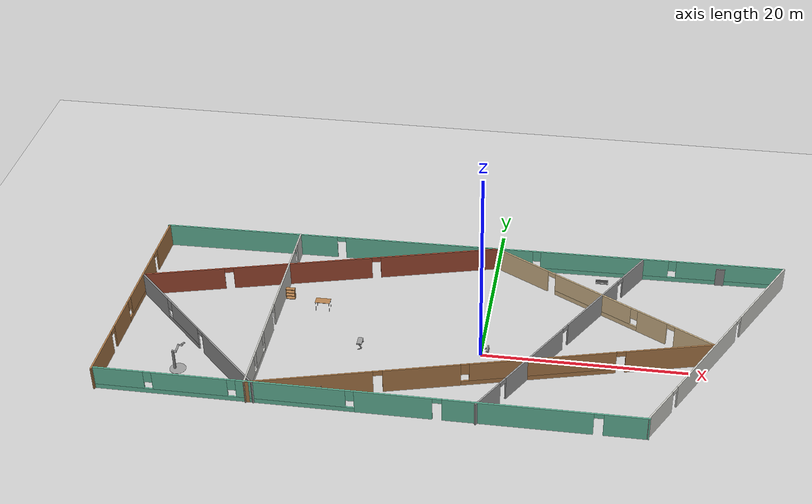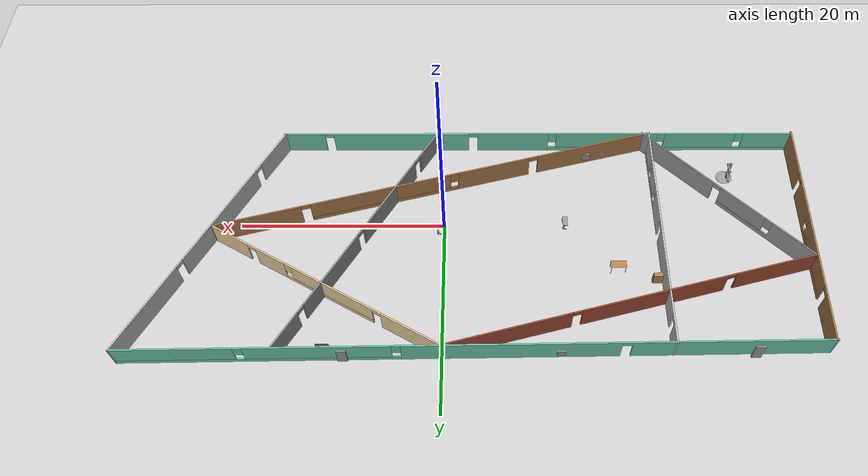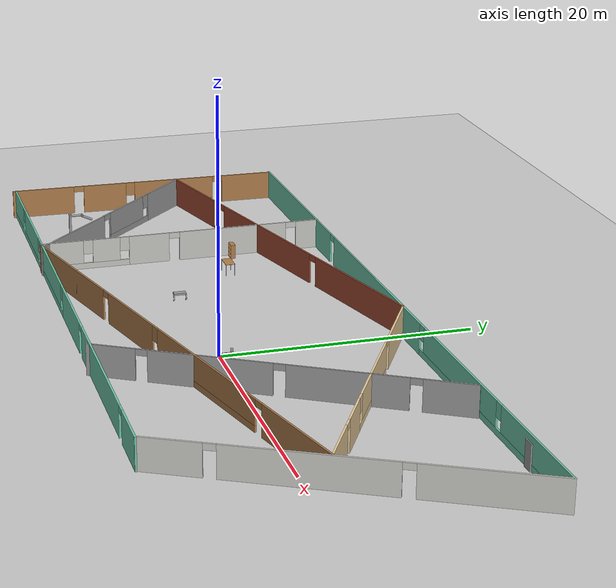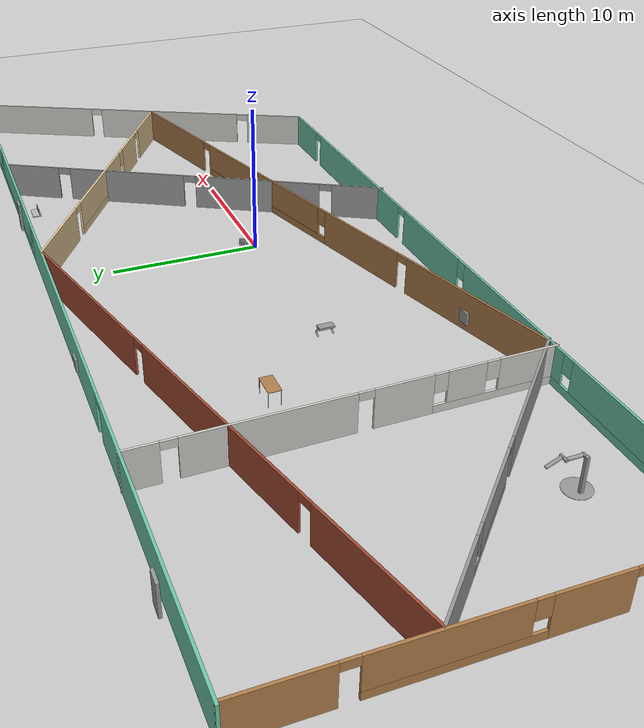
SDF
<sdf version="1.7">
 <world name="default">
  <light name="sun" type="directional">
   <pose>0 0 10 0 -0 0</pose>
   <diffuse>0.8 0.8 0.8 1</diffuse>
   <specular>0.2 0.2 0.2 1</specular>
   <attenuation>
    <range>1000</range>
    <constant>0.9</constant>
    <linear>0.01</linear>
    <quadratic>0.001</quadratic>
   </attenuation>
   <direction>-0.5 0.1 -0.9</direction>
   <spot><inner_angle>0</inner_angle><outer_angle>0</outer_angle><falloff>0</falloff></spot>
  </light>
  <model name="ground_plane">
   <static>1</static>
   <link name="link">
    <collision name="collision">
     <geometry><plane><normal>0 0 1</normal><size>100 100</size></plane></geometry>
     <surface>
      <contact><collide_bitmask>65535</collide_bitmask></contact>
      <friction><ode><mu>100</mu><mu2>50</mu2></ode></friction>
     </surface>
    </collision>
    <visual name="visual">
     <cast_shadows>0</cast_shadows>
     <geometry><plane><normal>0 0 1</normal><size>100 100</size></plane></geometry>
     <material>
      <script><uri>file://media/materials/scripts/gazebo.material</uri><name>Gazebo/Grey</name></script>
     </material>
    </visual>
   </link>
  </model>
  <gravity>0 0 -9.8</gravity>
  <magnetic_field>6e-06 2.3e-05 -4.2e-05</magnetic_field>
  <atmosphere type="adiabatic"/>
  <physics type="ode">
   <max_step_size>0.001</max_step_size>
   <real_time_factor>1</real_time_factor>
   <real_time_update_rate>1000</real_time_update_rate>
  </physics>
  <scene><ambient>0.4 0.4 0.4 1</ambient><background>0.7 0.7 0.7 1</background><shadows>1</shadows></scene>
  <spherical_coordinates>
   <surface_model>EARTH_WGS84</surface_model>
   <latitude_deg>0</latitude_deg>
   <longitude_deg>0</longitude_deg>
   <elevation>0</elevation>
   <heading_deg>0</heading_deg>
  </spherical_coordinates>
  <model name="HumanoidRobot">
   <link name="link_0">
    <inertial>
     <mass>1</mass>
     <inertia>
      <ixx>0.166667</ixx>
      <ixy>0</ixy>
      <ixz>0</ixz>
      <iyy>0.166667</iyy>
      <iyz>0</iyz>
      <izz>0.166667</izz>
     </inertia>
    </inertial>
    <pose>0.440203 -0.34659 0.542291 0 -0 0</pose>
    <visual name="visual">
     <geometry><box><size>0.5 1 0.15</size></box></geometry>
     <material>
      <lighting>1</lighting>
      <script><uri>file://media/materials/scripts/gazebo.material</uri><name>Gazebo/Grey</name></script>
      <shader type="pixel"><normal_map>__default__</normal_map></shader>
      <ambient>0.3 0.3 0.3 1</ambient>
      <diffuse>0.7 0.7 0.7 1</diffuse>
      <specular>0.01 0.01 0.01 1</specular>
      <emissive>0 0 0 1</emissive>
     </material>
    </visual>
    <collision name="collision">
     <geometry><box><size>0.5 1 0.15</size></box></geometry>
     <surface>
      <friction>
       <ode><mu>1</mu><mu2>1</mu2><fdir1>0 0 0</fdir1><slip1>0</slip1><slip2>0</slip2></ode>
       <torsional>
        <coefficient>1</coefficient>
        <patch_radius>0</patch_radius>
        <surface_radius>0</surface_radius>
        <use_patch_radius>1</use_patch_radius>
        <ode><slip>0</slip></ode>
       </torsional>
      </friction>
      <bounce><restitution_coefficient>0</restitution_coefficient><threshold>1e+06</threshold></bounce>
      <contact>
       <collide_without_contact>0</collide_without_contact>
       <collide_without_contact_bitmask>1</collide_without_contact_bitmask>
       <collide_bitmask>1</collide_bitmask>
       <ode>
        <soft_cfm>0</soft_cfm>
        <soft_erp>0.2</soft_erp>
        <kp>1e+13</kp>
        <kd>1</kd>
        <max_vel>0.01</max_vel>
        <min_depth>0</min_depth>
       </ode>
       <bullet>
        <split_impulse>1</split_impulse>
        <split_impulse_penetration_threshold>-0.01</split_impulse_penetration_threshold>
        <soft_cfm>0</soft_cfm>
        <soft_erp>0.2</soft_erp>
        <kp>1e+13</kp>
        <kd>1</kd>
       </bullet>
      </contact>
     </surface>
    </collision>
   </link>
   <link name="link_1">
    <inertial>
     <mass>1</mass>
     <inertia><ixx>0.145833</ixx><ixy>0</ixy><ixz>0</ixz><iyy>0.145833</iyy><iyz>0</iyz><izz>0.125</izz></inertia>
    </inertial>
    <pose>0.565203 -0.84659 0.325785 0 -0.523598 0</pose>
    <visual name="visual">
     <geometry><cylinder><radius>0.05</radius><length>0.5</length></cylinder></geometry>
     <material>
      <lighting>1</lighting>
      <script><uri>file://media/materials/scripts/gazebo.material</uri><name>Gazebo/Grey</name></script>
      <shader type="pixel"><normal_map>__default__</normal_map></shader>
      <ambient>0.3 0.3 0.3 1</ambient>
      <diffuse>0.7 0.7 0.7 1</diffuse>
      <specular>0.01 0.01 0.01 1</specular>
      <emissive>0 0 0 1</emissive>
     </material>
    </visual>
    <collision name="collision">
     <geometry><cylinder><radius>0.05</radius><length>0.5</length></cylinder></geometry>
     <surface>
      <friction>
       <ode><mu>1</mu><mu2>1</mu2><fdir1>0 0 0</fdir1><slip1>0</slip1><slip2>0</slip2></ode>
       <torsional>
        <coefficient>1</coefficient>
        <patch_radius>0</patch_radius>
        <surface_radius>0</surface_radius>
        <use_patch_radius>1</use_patch_radius>
        <ode><slip>0</slip></ode>
       </torsional>
      </friction>
      <bounce><restitution_coefficient>0</restitution_coefficient><threshold>1e+06</threshold></bounce>
      <contact>
       <collide_without_contact>0</collide_without_contact>
       <collide_without_contact_bitmask>1</collide_without_contact_bitmask>
       <collide_bitmask>1</collide_bitmask>
       <ode>
        <soft_cfm>0</soft_cfm>
        <soft_erp>0.2</soft_erp>
        <kp>1e+13</kp>
        <kd>1</kd>
        <max_vel>0.01</max_vel>
        <min_depth>0</min_depth>
       </ode>
       <bullet>
        <split_impulse>1</split_impulse>
        <split_impulse_penetration_threshold>-0.01</split_impulse_penetration_threshold>
        <soft_cfm>0</soft_cfm>
        <soft_erp>0.2</soft_erp>
        <kp>1e+13</kp>
        <kd>1</kd>
       </bullet>
      </contact>
     </surface>
    </collision>
   </link>
   <link name="link_1_clone">
    <inertial>
     <mass>1</mass>
     <inertia><ixx>0.145833</ixx><ixy>0</ixy><ixz>0</ixz><iyy>0.145833</iyy><iyz>0</iyz><izz>0.125</izz></inertia>
    </inertial>
    <pose>0.565203 0.15341 0.325785 0 -0.523598 0</pose>
    <visual name="visual">
     <geometry><cylinder><radius>0.05</radius><length>0.5</length></cylinder></geometry>
     <material>
      <lighting>1</lighting>
      <script><uri>file://media/materials/scripts/gazebo.material</uri><name>Gazebo/Grey</name></script>
      <shader type="pixel"><normal_map>__default__</normal_map></shader>
      <ambient>0.3 0.3 0.3 1</ambient>
      <diffuse>0.7 0.7 0.7 1</diffuse>
      <specular>0.01 0.01 0.01 1</specular>
      <emissive>0 0 0 1</emissive>
     </material>
    </visual>
    <collision name="collision">
     <geometry><cylinder><radius>0.05</radius><length>0.5</length></cylinder></geometry>
     <surface>
      <friction>
       <ode><mu>1</mu><mu2>1</mu2><fdir1>0 0 0</fdir1><slip1>0</slip1><slip2>0</slip2></ode>
       <torsional>
        <coefficient>1</coefficient>
        <patch_radius>0</patch_radius>
        <surface_radius>0</surface_radius>
        <use_patch_radius>1</use_patch_radius>
        <ode><slip>0</slip></ode>
       </torsional>
      </friction>
      <bounce><restitution_coefficient>0</restitution_coefficient><threshold>1e+06</threshold></bounce>
      <contact>
       <collide_without_contact>0</collide_without_contact>
       <collide_without_contact_bitmask>1</collide_without_contact_bitmask>
       <collide_bitmask>1</collide_bitmask>
       <ode>
        <soft_cfm>0</soft_cfm>
        <soft_erp>0.2</soft_erp>
        <kp>1e+13</kp>
        <kd>1</kd>
        <max_vel>0.01</max_vel>
        <min_depth>0</min_depth>
       </ode>
       <bullet>
        <split_impulse>1</split_impulse>
        <split_impulse_penetration_threshold>-0.01</split_impulse_penetration_threshold>
        <soft_cfm>0</soft_cfm>
        <soft_erp>0.2</soft_erp>
        <kp>1e+13</kp>
        <kd>1</kd>
       </bullet>
      </contact>
     </surface>
    </collision>
   </link>
   <link name="link_1_clone_0">
    <inertial>
     <mass>1</mass>
     <inertia><ixx>0.145833</ixx><ixy>0</ixy><ixz>0</ixz><iyy>0.145833</iyy><iyz>0</iyz><izz>0.125</izz></inertia>
    </inertial>
    <pose>0.473697 -0.84659 -0.015721 0 1.0472 0</pose>
    <visual name="visual">
     <geometry><cylinder><radius>0.05</radius><length>0.5</length></cylinder></geometry>
     <material>
      <lighting>1</lighting>
      <script><uri>file://media/materials/scripts/gazebo.material</uri><name>Gazebo/Grey</name></script>
      <shader type="pixel"><normal_map>__default__</normal_map></shader>
      <ambient>0.3 0.3 0.3 1</ambient>
      <diffuse>0.7 0.7 0.7 1</diffuse>
      <specular>0.01 0.01 0.01 1</specular>
      <emissive>0 0 0 1</emissive>
     </material>
    </visual>
    <collision name="collision">
     <geometry><cylinder><radius>0.05</radius><length>0.5</length></cylinder></geometry>
     <surface>
      <friction>
       <ode><mu>1</mu><mu2>1</mu2><fdir1>0 0 0</fdir1><slip1>0</slip1><slip2>0</slip2></ode>
       <torsional>
        <coefficient>1</coefficient>
        <patch_radius>0</patch_radius>
        <surface_radius>0</surface_radius>
        <use_patch_radius>1</use_patch_radius>
        <ode><slip>0</slip></ode>
       </torsional>
      </friction>
      <bounce><restitution_coefficient>0</restitution_coefficient><threshold>1e+06</threshold></bounce>
      <contact>
       <collide_without_contact>0</collide_without_contact>
       <collide_without_contact_bitmask>1</collide_without_contact_bitmask>
       <collide_bitmask>1</collide_bitmask>
       <ode>
        <soft_cfm>0</soft_cfm>
        <soft_erp>0.2</soft_erp>
        <kp>1e+13</kp>
        <kd>1</kd>
        <max_vel>0.01</max_vel>
        <min_depth>0</min_depth>
       </ode>
       <bullet>
        <split_impulse>1</split_impulse>
        <split_impulse_penetration_threshold>-0.01</split_impulse_penetration_threshold>
        <soft_cfm>0</soft_cfm>
        <soft_erp>0.2</soft_erp>
        <kp>1e+13</kp>
        <kd>1</kd>
       </bullet>
      </contact>
     </surface>
    </collision>
   </link>
   <link name="link_1_clone_0_clone">
    <inertial>
     <mass>1</mass>
     <inertia><ixx>0.145833</ixx><ixy>0</ixy><ixz>0</ixz><iyy>0.145833</iyy><iyz>0</iyz><izz>0.125</izz></inertia>
    </inertial>
    <pose>0.473697 0.15341 -0.015721 0 1.0472 0</pose>
    <visual name="visual">
     <geometry><cylinder><radius>0.05</radius><length>0.5</length></cylinder></geometry>
     <material>
      <lighting>1</lighting>
      <script><uri>file://media/materials/scripts/gazebo.material</uri><name>Gazebo/Grey</name></script>
      <shader type="pixel"><normal_map>__default__</normal_map></shader>
      <ambient>0.3 0.3 0.3 1</ambient>
      <diffuse>0.7 0.7 0.7 1</diffuse>
      <specular>0.01 0.01 0.01 1</specular>
      <emissive>0 0 0 1</emissive>
     </material>
    </visual>
    <collision name="collision">
     <geometry><cylinder><radius>0.05</radius><length>0.5</length></cylinder></geometry>
     <surface>
      <friction>
       <ode><mu>1</mu><mu2>1</mu2><fdir1>0 0 0</fdir1><slip1>0</slip1><slip2>0</slip2></ode>
       <torsional>
        <coefficient>1</coefficient>
        <patch_radius>0</patch_radius>
        <surface_radius>0</surface_radius>
        <use_patch_radius>1</use_patch_radius>
        <ode><slip>0</slip></ode>
       </torsional>
      </friction>
      <bounce><restitution_coefficient>0</restitution_coefficient><threshold>1e+06</threshold></bounce>
      <contact>
       <collide_without_contact>0</collide_without_contact>
       <collide_without_contact_bitmask>1</collide_without_contact_bitmask>
       <collide_bitmask>1</collide_bitmask>
       <ode>
        <soft_cfm>0</soft_cfm>
        <soft_erp>0.2</soft_erp>
        <kp>1e+13</kp>
        <kd>1</kd>
        <max_vel>0.01</max_vel>
        <min_depth>0</min_depth>
       </ode>
       <bullet>
        <split_impulse>1</split_impulse>
        <split_impulse_penetration_threshold>-0.01</split_impulse_penetration_threshold>
        <soft_cfm>0</soft_cfm>
        <soft_erp>0.2</soft_erp>
        <kp>1e+13</kp>
        <kd>1</kd>
       </bullet>
      </contact>
     </surface>
    </collision>
   </link>
   <link name="link_2">
    <inertial>
     <mass>1</mass>
     <inertia>
      <ixx>0.166667</ixx>
      <ixy>0</ixy>
      <ixz>0</ixz>
      <iyy>0.166667</iyy>
      <iyz>0</iyz>
      <izz>0.166667</izz>
     </inertia>
    </inertial>
    <pose>0.320604 -0.84659 -0.104109 0 -0 0</pose>
    <visual name="visual">
     <geometry><box><size>0.5 0.2 0.05</size></box></geometry>
     <material>
      <lighting>1</lighting>
      <script><uri>file://media/materials/scripts/gazebo.material</uri><name>Gazebo/Grey</name></script>
      <shader type="pixel"><normal_map>__default__</normal_map></shader>
      <ambient>0.3 0.3 0.3 1</ambient>
      <diffuse>0.7 0.7 0.7 1</diffuse>
      <specular>0.01 0.01 0.01 1</specular>
      <emissive>0 0 0 1</emissive>
     </material>
    </visual>
    <collision name="collision">
     <geometry><box><size>0.5 0.25 0.05</size></box></geometry>
     <surface>
      <friction>
       <ode><mu>1</mu><mu2>1</mu2><fdir1>0 0 0</fdir1><slip1>0</slip1><slip2>0</slip2></ode>
       <torsional>
        <coefficient>1</coefficient>
        <patch_radius>0</patch_radius>
        <surface_radius>0</surface_radius>
        <use_patch_radius>1</use_patch_radius>
        <ode><slip>0</slip></ode>
       </torsional>
      </friction>
      <bounce><restitution_coefficient>0</restitution_coefficient><threshold>1e+06</threshold></bounce>
      <contact>
       <collide_without_contact>0</collide_without_contact>
       <collide_without_contact_bitmask>1</collide_without_contact_bitmask>
       <collide_bitmask>1</collide_bitmask>
       <ode>
        <soft_cfm>0</soft_cfm>
        <soft_erp>0.2</soft_erp>
        <kp>1e+13</kp>
        <kd>1</kd>
        <max_vel>0.01</max_vel>
        <min_depth>0</min_depth>
       </ode>
       <bullet>
        <split_impulse>1</split_impulse>
        <split_impulse_penetration_threshold>-0.01</split_impulse_penetration_threshold>
        <soft_cfm>0</soft_cfm>
        <soft_erp>0.2</soft_erp>
        <kp>1e+13</kp>
        <kd>1</kd>
       </bullet>
      </contact>
     </surface>
    </collision>
   </link>
   <link name="link_2_clone">
    <inertial>
     <mass>1</mass>
     <inertia>
      <ixx>0.166667</ixx>
      <ixy>0</ixy>
      <ixz>0</ixz>
      <iyy>0.166667</iyy>
      <iyz>0</iyz>
      <izz>0.166667</izz>
     </inertia>
    </inertial>
    <pose>0.320604 0.15341 -0.104109 0 -0 0</pose>
    <visual name="visual">
     <geometry><box><size>0.5 0.2 0.05</size></box></geometry>
     <material>
      <lighting>1</lighting>
      <script><uri>file://media/materials/scripts/gazebo.material</uri><name>Gazebo/Grey</name></script>
      <shader type="pixel"><normal_map>__default__</normal_map></shader>
      <ambient>0.3 0.3 0.3 1</ambient>
      <diffuse>0.7 0.7 0.7 1</diffuse>
      <specular>0.01 0.01 0.01 1</specular>
      <emissive>0 0 0 1</emissive>
     </material>
    </visual>
    <collision name="collision">
     <geometry><box><size>0.5 0.25 0.05</size></box></geometry>
     <surface>
      <friction>
       <ode><mu>1</mu><mu2>1</mu2><fdir1>0 0 0</fdir1><slip1>0</slip1><slip2>0</slip2></ode>
       <torsional>
        <coefficient>1</coefficient>
        <patch_radius>0</patch_radius>
        <surface_radius>0</surface_radius>
        <use_patch_radius>1</use_patch_radius>
        <ode><slip>0</slip></ode>
       </torsional>
      </friction>
      <bounce><restitution_coefficient>0</restitution_coefficient><threshold>1e+06</threshold></bounce>
      <contact>
       <collide_without_contact>0</collide_without_contact>
       <collide_without_contact_bitmask>1</collide_without_contact_bitmask>
       <collide_bitmask>1</collide_bitmask>
       <ode>
        <soft_cfm>0</soft_cfm>
        <soft_erp>0.2</soft_erp>
        <kp>1e+13</kp>
        <kd>1</kd>
        <max_vel>0.01</max_vel>
        <min_depth>0</min_depth>
       </ode>
       <bullet>
        <split_impulse>1</split_impulse>
        <split_impulse_penetration_threshold>-0.01</split_impulse_penetration_threshold>
        <soft_cfm>0</soft_cfm>
        <soft_erp>0.2</soft_erp>
        <kp>1e+13</kp>
        <kd>1</kd>
       </bullet>
      </contact>
     </surface>
    </collision>
   </link>
   <joint name="link_0_JOINT_4" type="revolute">
    <parent>link_0</parent>
    <child>link_1</child>
    <pose>0 0 0.25 0 -0 0</pose>
    <axis>
     <xyz>1 0 0</xyz>
     <limit>
      <lower>-1.79769e+308</lower>
      <upper>1.79769e+308</upper>
      <effort>-1</effort>
      <velocity>-1</velocity>
     </limit>
     <dynamics>
      <spring_reference>0</spring_reference>
      <spring_stiffness>0</spring_stiffness>
      <damping>0</damping>
     </dynamics>
    </axis>
    <physics>
     <ode><limit><cfm>0</cfm><erp>0.2</erp></limit><suspension><cfm>0</cfm><erp>0.2</erp></suspension></ode>
    </physics>
   </joint>
   <joint name="link_0_JOINT_5" type="revolute">
    <parent>link_0</parent>
    <child>link_1_clone</child>
    <pose>0 0 0.25 0 -0 0</pose>
    <axis>
     <xyz>1 0 0</xyz>
     <limit>
      <lower>-1.79769e+308</lower>
      <upper>1.79769e+308</upper>
      <effort>-1</effort>
      <velocity>-1</velocity>
     </limit>
     <dynamics>
      <spring_reference>0</spring_reference>
      <spring_stiffness>0</spring_stiffness>
      <damping>0</damping>
     </dynamics>
    </axis>
    <physics>
     <ode><limit><cfm>0</cfm><erp>0.2</erp></limit><suspension><cfm>0</cfm><erp>0.2</erp></suspension></ode>
    </physics>
   </joint>
   <joint name="link_1_JOINT_6" type="revolute">
    <parent>link_1</parent>
    <child>link_1_clone_0</child>
    <pose>0 0 0.25 -0.02 0 0</pose>
    <axis>
     <xyz>1 0 0</xyz>
     <limit>
      <lower>-1.79769e+308</lower>
      <upper>1.79769e+308</upper>
      <effort>-1</effort>
      <velocity>-1</velocity>
     </limit>
     <dynamics>
      <spring_reference>0</spring_reference>
      <spring_stiffness>0</spring_stiffness>
      <damping>0</damping>
     </dynamics>
    </axis>
    <physics>
     <ode><limit><cfm>0</cfm><erp>0.2</erp></limit><suspension><cfm>0</cfm><erp>0.2</erp></suspension></ode>
    </physics>
   </joint>
   <joint name="link_1_clone_0_JOINT_8" type="revolute">
    <parent>link_1_clone_0</parent>
    <child>link_2</child>
    <axis>
     <xyz>1 0 0</xyz>
     <limit>
      <lower>-1.79769e+308</lower>
      <upper>1.79769e+308</upper>
      <effort>-1</effort>
      <velocity>-1</velocity>
     </limit>
     <dynamics>
      <spring_reference>0</spring_reference>
      <spring_stiffness>0</spring_stiffness>
      <damping>0</damping>
     </dynamics>
    </axis>
    <physics>
     <ode><limit><cfm>0</cfm><erp>0.2</erp></limit><suspension><cfm>0</cfm><erp>0.2</erp></suspension></ode>
    </physics>
   </joint>
   <joint name="link_1_clone_0_clone_JOINT_9" type="revolute">
    <parent>link_1_clone_0_clone</parent>
    <child>link_2_clone</child>
    <axis>
     <xyz>1 0 0</xyz>
     <limit>
      <lower>-1.79769e+308</lower>
      <upper>1.79769e+308</upper>
      <effort>-1</effort>
      <velocity>-1</velocity>
     </limit>
     <dynamics>
      <spring_reference>0</spring_reference>
      <spring_stiffness>0</spring_stiffness>
      <damping>0</damping>
     </dynamics>
    </axis>
    <physics>
     <ode><limit><cfm>0</cfm><erp>0.2</erp></limit><suspension><cfm>0</cfm><erp>0.2</erp></suspension></ode>
    </physics>
   </joint>
   <joint name="link_1_clone_JOINT_7" type="revolute">
    <parent>link_1_clone</parent>
    <child>link_1_clone_0_clone</child>
    <pose>0 0 0.25 0 -0 0</pose>
    <axis>
     <xyz>1 0 0</xyz>
     <limit>
      <lower>-1.79769e+308</lower>
      <upper>1.79769e+308</upper>
      <effort>-1</effort>
      <velocity>-1</velocity>
     </limit>
     <dynamics>
      <spring_reference>0</spring_reference>
      <spring_stiffness>0</spring_stiffness>
      <damping>0</damping>
     </dynamics>
    </axis>
    <physics>
     <ode><limit><cfm>0</cfm><erp>0.2</erp></limit><suspension><cfm>0</cfm><erp>0.2</erp></suspension></ode>
    </physics>
   </joint>
   <static>0</static>
   <pose>0.039153 0.816059 0.644116 -1.7e-05 1.47835 -0.027882</pose>
  </model>
  <model name="Building">
   <pose>-3.14962 2.4136 0 0 -0 0</pose>
   <link name="Door_0">
    <collision name="Door_0_Collision">
     <geometry><box><size>0.9 0.17 2</size></box></geometry>
     <pose>0 0 1 0 -0 0</pose>
    </collision>
    <visual name="Door_0_Visual">
     <pose>0 0 1 0 -0 0</pose>
     <geometry><box><size>0.9 0.17 2</size></box></geometry>
     <material>
      <script><uri>file://media/materials/scripts/gazebo.material</uri><name>Gazebo/Grey</name></script>
     </material>
    </visual>
    <pose>-25.1642 11.9657 0 0 -0 0</pose>
   </link>
   <link name="Door_19">
    <collision name="Door_19_Collision">
     <geometry><box><size>0.9 0.17 2</size></box></geometry>
     <pose>0 0 1 0 -0 0</pose>
    </collision>
    <visual name="Door_19_Visual">
     <pose>0 0 1 0 -0 0</pose>
     <geometry><box><size>0.9 0.17 2</size></box></geometry>
     <material>
      <script><uri>file://media/materials/scripts/gazebo.material</uri><name>Gazebo/Grey</name></script>
     </material>
    </visual>
    <pose>26.0112 12.2744 0 0 -0 0</pose>
   </link>
   <link name="Door_25">
    <collision name="Door_25_Collision">
     <geometry><box><size>0.9 0.17 2</size></box></geometry>
     <pose>0 0 1 0 -0 0</pose>
    </collision>
    <visual name="Door_25_Visual">
     <pose>0 0 1 0 -0 0</pose>
     <geometry><box><size>0.9 0.17 2</size></box></geometry>
     <material>
      <script><uri>file://media/materials/scripts/gazebo.material</uri><name>Gazebo/Grey</name></script>
     </material>
    </visual>
    <pose>12.012 12.3054 0 0 -0 0</pose>
   </link>
   <link name="Wall_0">
    <pose>-32.1052 -0.483581 0 0 -0 1.54834</pose>
    <visual name="Wall_0_Visual_0">
     <pose>-9.26842 0 1.25 0 -0 0</pose>
     <geometry><box><size>5.57682 0.15 2.5</size></box></geometry>
     <material>
      <script><uri>file://media/materials/scripts/gazebo.material</uri><name>Gazebo/Wood</name></script>
      <ambient>1 1 1 1</ambient>
     </material>
     <meta><layer>0</layer></meta>
    </visual>
    <collision name="Wall_0_Collision_0">
     <geometry><box><size>5.57682 0.15 2.5</size></box></geometry>
     <pose>-9.26842 0 1.25 0 -0 0</pose>
    </collision>
    <visual name="Wall_0_Visual_1">
     <pose>-3.61912 0 1.25 0 -0 0</pose>
     <geometry><box><size>3.92177 0.15 2.5</size></box></geometry>
     <material>
      <script><uri>file://media/materials/scripts/gazebo.material</uri><name>Gazebo/Wood</name></script>
      <ambient>1 1 1 1</ambient>
     </material>
     <meta><layer>0</layer></meta>
    </visual>
    <collision name="Wall_0_Collision_1">
     <geometry><box><size>3.92177 0.15 2.5</size></box></geometry>
     <pose>-3.61912 0 1.25 0 -0 0</pose>
    </collision>
    <visual name="Wall_0_Visual_2">
     <pose>9.71831 0 1.25 0 -0 0</pose>
     <geometry><box><size>4.67703 0.15 2.5</size></box></geometry>
     <material>
      <script><uri>file://media/materials/scripts/gazebo.material</uri><name>Gazebo/Wood</name></script>
      <ambient>1 1 1 1</ambient>
     </material>
     <meta><layer>0</layer></meta>
    </visual>
    <collision name="Wall_0_Collision_2">
     <geometry><box><size>4.67703 0.15 2.5</size></box></geometry>
     <pose>9.71831 0 1.25 0 -0 0</pose>
    </collision>
    <visual name="Wall_0_Visual_3">
     <pose>2.41078 0 0.25 0 -0 0</pose>
     <geometry><box><size>8.13804 0.15 0.5</size></box></geometry>
     <material>
      <script><uri>file://media/materials/scripts/gazebo.material</uri><name>Gazebo/Wood</name></script>
      <ambient>1 1 1 1</ambient>
     </material>
     <meta><layer>0</layer></meta>
    </visual>
    <collision name="Wall_0_Collision_3">
     <geometry><box><size>8.13804 0.15 0.5</size></box></geometry>
     <pose>2.41078 0 0.25 0 -0 0</pose>
    </collision>
    <visual name="Wall_0_Visual_4">
     <pose>2.81078 0 1.5 0 -0 0</pose>
     <geometry><box><size>7.33803 0.15 2</size></box></geometry>
     <material>
      <script><uri>file://media/materials/scripts/gazebo.material</uri><name>Gazebo/Wood</name></script>
      <ambient>1 1 1 1</ambient>
     </material>
     <meta><layer>0</layer></meta>
    </visual>
    <collision name="Wall_0_Collision_4">
     <geometry><box><size>7.33803 0.15 2</size></box></geometry>
     <pose>2.81078 0 1.5 0 -0 0</pose>
    </collision>
    <visual name="Wall_0_Visual_5">
     <pose>-1.25824 0 1.9 0 -0 0</pose>
     <geometry><box><size>0.8 0.15 1.2</size></box></geometry>
     <material>
      <script><uri>file://media/materials/scripts/gazebo.material</uri><name>Gazebo/Wood</name></script>
      <ambient>1 1 1 1</ambient>
     </material>
     <meta><layer>0</layer></meta>
    </visual>
    <collision name="Wall_0_Collision_5">
     <geometry><box><size>0.8 0.15 1.2</size></box></geometry>
     <pose>-1.25824 0 1.9 0 -0 0</pose>
    </collision>
    <visual name="Wall_0_Visual_6">
     <pose>-6.03001 0 2.25 0 -0 0</pose>
     <geometry><box><size>0.9 0.15 0.5</size></box></geometry>
     <material>
      <script><uri>file://media/materials/scripts/gazebo.material</uri><name>Gazebo/Wood</name></script>
      <ambient>1 1 1 1</ambient>
     </material>
     <meta><layer>0</layer></meta>
    </visual>
    <collision name="Wall_0_Collision_6">
     <geometry><box><size>0.9 0.15 0.5</size></box></geometry>
     <pose>-6.03001 0 2.25 0 -0 0</pose>
    </collision>
    <visual name="Wall_0_Visual_7">
     <pose>6.9298 0 2.25 0 -0 0</pose>
     <geometry><box><size>0.9 0.15 0.5</size></box></geometry>
     <material>
      <script><uri>file://media/materials/scripts/gazebo.material</uri><name>Gazebo/Wood</name></script>
      <ambient>1 1 1 1</ambient>
     </material>
     <meta><layer>0</layer></meta>
    </visual>
    <collision name="Wall_0_Collision_7">
     <geometry><box><size>0.9 0.15 0.5</size></box></geometry>
     <pose>6.9298 0 2.25 0 -0 0</pose>
    </collision>
   </link>
   <link name="Wall_1">
    <pose>0.1492 11.9795 0 0 -0 0.015088</pose>
    <visual name="Wall_1_Visual_0">
     <pose>-23.0722 0 1.25 0 -0 0</pose>
     <geometry><box><size>18.1988 0.15 2.5</size></box></geometry>
     <material>
      <script><uri>file://media/materials/scripts/gazebo.material</uri><name>Gazebo/Grey</name></script>
      <ambient>0.435294 0.796078 0.67451 1</ambient>
     </material>
     <meta><layer>0</layer></meta>
    </visual>
    <collision name="Wall_1_Collision_0">
     <geometry><box><size>18.1988 0.15 2.5</size></box></geometry>
     <pose>-23.0722 0 1.25 0 -0 0</pose>
    </collision>
    <visual name="Wall_1_Visual_1">
     <pose>-3.237 0 1.25 0 -0 0</pose>
     <geometry><box><size>19.6716 0.15 2.5</size></box></geometry>
     <material>
      <script><uri>file://media/materials/scripts/gazebo.material</uri><name>Gazebo/Grey</name></script>
      <ambient>0.435294 0.796078 0.67451 1</ambient>
     </material>
     <meta><layer>0</layer></meta>
    </visual>
    <collision name="Wall_1_Collision_1">
     <geometry><box><size>19.6716 0.15 2.5</size></box></geometry>
     <pose>-3.237 0 1.25 0 -0 0</pose>
    </collision>
    <visual name="Wall_1_Visual_2">
     <pose>19.3852 0 0.25 0 -0 0</pose>
     <geometry><box><size>25.5729 0.15 0.5</size></box></geometry>
     <material>
      <script><uri>file://media/materials/scripts/gazebo.material</uri><name>Gazebo/Grey</name></script>
      <ambient>0.435294 0.796078 0.67451 1</ambient>
     </material>
     <meta><layer>0</layer></meta>
    </visual>
    <collision name="Wall_1_Collision_2">
     <geometry><box><size>25.5729 0.15 0.5</size></box></geometry>
     <pose>19.3852 0 0.25 0 -0 0</pose>
    </collision>
    <visual name="Wall_1_Visual_3">
     <pose>13.974 0 1.5 0 -0 0</pose>
     <geometry><box><size>13.1505 0.15 2</size></box></geometry>
     <material>
      <script><uri>file://media/materials/scripts/gazebo.material</uri><name>Gazebo/Grey</name></script>
      <ambient>0.435294 0.796078 0.67451 1</ambient>
     </material>
     <meta><layer>0</layer></meta>
    </visual>
    <collision name="Wall_1_Collision_3">
     <geometry><box><size>13.1505 0.15 2</size></box></geometry>
     <pose>13.974 0 1.5 0 -0 0</pose>
    </collision>
    <visual name="Wall_1_Visual_4">
     <pose>26.7605 0 1.5 0 -0 0</pose>
     <geometry><box><size>10.8224 0.15 2</size></box></geometry>
     <material>
      <script><uri>file://media/materials/scripts/gazebo.material</uri><name>Gazebo/Grey</name></script>
      <ambient>0.435294 0.796078 0.67451 1</ambient>
     </material>
     <meta><layer>0</layer></meta>
    </visual>
    <collision name="Wall_1_Collision_4">
     <geometry><box><size>10.8224 0.15 2</size></box></geometry>
     <pose>26.7605 0 1.5 0 -0 0</pose>
    </collision>
    <visual name="Wall_1_Visual_5">
     <pose>6.9988 0 1.9 0 -0 0</pose>
     <geometry><box><size>0.8 0.15 1.2</size></box></geometry>
     <material>
      <script><uri>file://media/materials/scripts/gazebo.material</uri><name>Gazebo/Grey</name></script>
      <ambient>0.435294 0.796078 0.67451 1</ambient>
     </material>
     <meta><layer>0</layer></meta>
    </visual>
    <collision name="Wall_1_Collision_5">
     <geometry><box><size>0.8 0.15 1.2</size></box></geometry>
     <pose>6.9988 0 1.9 0 -0 0</pose>
    </collision>
    <visual name="Wall_1_Visual_6">
     <pose>20.9493 0 1.9 0 -0 0</pose>
     <geometry><box><size>0.8 0.15 1.2</size></box></geometry>
     <material>
      <script><uri>file://media/materials/scripts/gazebo.material</uri><name>Gazebo/Grey</name></script>
      <ambient>0.435294 0.796078 0.67451 1</ambient>
     </material>
     <meta><layer>0</layer></meta>
    </visual>
    <collision name="Wall_1_Collision_6">
     <geometry><box><size>0.8 0.15 1.2</size></box></geometry>
     <pose>20.9493 0 1.9 0 -0 0</pose>
    </collision>
    <visual name="Wall_1_Visual_7">
     <pose>-13.5228 0 2.25 0 -0 0</pose>
     <geometry><box><size>0.9 0.15 0.5</size></box></geometry>
     <material>
      <script><uri>file://media/materials/scripts/gazebo.material</uri><name>Gazebo/Grey</name></script>
      <ambient>0.435294 0.796078 0.67451 1</ambient>
     </material>
     <meta><layer>0</layer></meta>
    </visual>
    <collision name="Wall_1_Collision_7">
     <geometry><box><size>0.9 0.15 0.5</size></box></geometry>
     <pose>-13.5228 0 2.25 0 -0 0</pose>
    </collision>
   </link>
   <link name="Wall_11">
    <pose>10.9787 -0.186477 0 0 -0 1.0472</pose>
    <visual name="Wall_11_Visual_0">
     <pose>-12.3766 0 1.25 0 -0 0</pose>
     <geometry><box><size>3.74686 0.15 2.5</size></box></geometry>
     <material>
      <script><uri>file://media/materials/scripts/gazebo.material</uri><name>Gazebo/Grey</name></script>
      <ambient>1 1 1 1</ambient>
     </material>
     <meta><layer>0</layer></meta>
    </visual>
    <collision name="Wall_11_Collision_0">
     <geometry><box><size>3.74686 0.15 2.5</size></box></geometry>
     <pose>-12.3766 0 1.25 0 -0 0</pose>
    </collision>
    <visual name="Wall_11_Visual_1">
     <pose>-4.96596 0 1.25 0 -0 0</pose>
     <geometry><box><size>9.27435 0.15 2.5</size></box></geometry>
     <material>
      <script><uri>file://media/materials/scripts/gazebo.material</uri><name>Gazebo/Grey</name></script>
      <ambient>1 1 1 1</ambient>
     </material>
     <meta><layer>0</layer></meta>
    </visual>
    <collision name="Wall_11_Collision_1">
     <geometry><box><size>9.27435 0.15 2.5</size></box></geometry>
     <pose>-4.96596 0 1.25 0 -0 0</pose>
    </collision>
    <visual name="Wall_11_Visual_2">
     <pose>4.98582 0 1.25 0 -0 0</pose>
     <geometry><box><size>8.82921 0.15 2.5</size></box></geometry>
     <material>
      <script><uri>file://media/materials/scripts/gazebo.material</uri><name>Gazebo/Grey</name></script>
      <ambient>1 1 1 1</ambient>
     </material>
     <meta><layer>0</layer></meta>
    </visual>
    <collision name="Wall_11_Collision_2">
     <geometry><box><size>8.82921 0.15 2.5</size></box></geometry>
     <pose>4.98582 0 1.25 0 -0 0</pose>
    </collision>
    <visual name="Wall_11_Visual_3">
     <pose>12.2752 0 1.25 0 -0 0</pose>
     <geometry><box><size>3.94958 0.15 2.5</size></box></geometry>
     <material>
      <script><uri>file://media/materials/scripts/gazebo.material</uri><name>Gazebo/Grey</name></script>
      <ambient>1 1 1 1</ambient>
     </material>
     <meta><layer>0</layer></meta>
    </visual>
    <collision name="Wall_11_Collision_3">
     <geometry><box><size>3.94958 0.15 2.5</size></box></geometry>
     <pose>12.2752 0 1.25 0 -0 0</pose>
    </collision>
    <visual name="Wall_11_Visual_4">
     <pose>-10.0531 0 2.25 0 -0 0</pose>
     <geometry><box><size>0.9 0.15 0.5</size></box></geometry>
     <material>
      <script><uri>file://media/materials/scripts/gazebo.material</uri><name>Gazebo/Grey</name></script>
      <ambient>1 1 1 1</ambient>
     </material>
     <meta><layer>0</layer></meta>
    </visual>
    <collision name="Wall_11_Collision_4">
     <geometry><box><size>0.9 0.15 0.5</size></box></geometry>
     <pose>-10.0531 0 2.25 0 -0 0</pose>
    </collision>
    <visual name="Wall_11_Visual_5">
     <pose>0.121212 0 2.25 0 -0 0</pose>
     <geometry><box><size>0.9 0.15 0.5</size></box></geometry>
     <material>
      <script><uri>file://media/materials/scripts/gazebo.material</uri><name>Gazebo/Grey</name></script>
      <ambient>1 1 1 1</ambient>
     </material>
     <meta><layer>0</layer></meta>
    </visual>
    <collision name="Wall_11_Collision_5">
     <geometry><box><size>0.9 0.15 0.5</size></box></geometry>
     <pose>0.121212 0 2.25 0 -0 0</pose>
    </collision>
    <visual name="Wall_11_Visual_6">
     <pose>9.85042 0 2.25 0 -0 0</pose>
     <geometry><box><size>0.9 0.15 0.5</size></box></geometry>
     <material>
      <script><uri>file://media/materials/scripts/gazebo.material</uri><name>Gazebo/Grey</name></script>
      <ambient>1 1 1 1</ambient>
     </material>
     <meta><layer>0</layer></meta>
    </visual>
    <collision name="Wall_11_Collision_6">
     <geometry><box><size>0.9 0.15 0.5</size></box></geometry>
     <pose>9.85042 0 2.25 0 -0 0</pose>
    </collision>
   </link>
   <link name="Wall_2">
    <pose>25.9469 0.109933 0 0 -0 -2.04897</pose>
    <visual name="Wall_2_Visual_0">
     <pose>-9.11112 0 1.25 0 -0 0</pose>
     <geometry><box><size>9.75682 0.15 2.5</size></box></geometry>
     <material>
      <script><uri>file://media/materials/scripts/gazebo.material</uri><name>Gazebo/CeilingTiled</name></script>
      <ambient>1 1 1 1</ambient>
     </material>
     <meta><layer>0</layer></meta>
    </visual>
    <collision name="Wall_2_Collision_0">
     <geometry><box><size>9.75682 0.15 2.5</size></box></geometry>
     <pose>-9.11112 0 1.25 0 -0 0</pose>
    </collision>
    <visual name="Wall_2_Visual_1">
     <pose>2.60929 0 1.25 0 -0 0</pose>
     <geometry><box><size>11.884 0.15 2.5</size></box></geometry>
     <material>
      <script><uri>file://media/materials/scripts/gazebo.material</uri><name>Gazebo/CeilingTiled</name></script>
      <ambient>1 1 1 1</ambient>
     </material>
     <meta><layer>0</layer></meta>
    </visual>
    <collision name="Wall_2_Collision_1">
     <geometry><box><size>11.884 0.15 2.5</size></box></geometry>
     <pose>2.60929 0 1.25 0 -0 0</pose>
    </collision>
    <visual name="Wall_2_Visual_2">
     <pose>11.7204 0 1.25 0 -0 0</pose>
     <geometry><box><size>4.53824 0.15 2.5</size></box></geometry>
     <material>
      <script><uri>file://media/materials/scripts/gazebo.material</uri><name>Gazebo/CeilingTiled</name></script>
      <ambient>1 1 1 1</ambient>
     </material>
     <meta><layer>0</layer></meta>
    </visual>
    <collision name="Wall_2_Collision_2">
     <geometry><box><size>4.53824 0.15 2.5</size></box></geometry>
     <pose>11.7204 0 1.25 0 -0 0</pose>
    </collision>
    <visual name="Wall_2_Visual_3">
     <pose>-3.78271 0 2.25 0 -0 0</pose>
     <geometry><box><size>0.9 0.15 0.5</size></box></geometry>
     <material>
      <script><uri>file://media/materials/scripts/gazebo.material</uri><name>Gazebo/CeilingTiled</name></script>
      <ambient>1 1 1 1</ambient>
     </material>
     <meta><layer>0</layer></meta>
    </visual>
    <collision name="Wall_2_Collision_3">
     <geometry><box><size>0.9 0.15 0.5</size></box></geometry>
     <pose>-3.78271 0 2.25 0 -0 0</pose>
    </collision>
    <visual name="Wall_2_Visual_4">
     <pose>9.0013 0 2.25 0 -0 0</pose>
     <geometry><box><size>0.9 0.15 0.5</size></box></geometry>
     <material>
      <script><uri>file://media/materials/scripts/gazebo.material</uri><name>Gazebo/CeilingTiled</name></script>
      <ambient>1 1 1 1</ambient>
     </material>
     <meta><layer>0</layer></meta>
    </visual>
    <collision name="Wall_2_Collision_4">
     <geometry><box><size>0.9 0.15 0.5</size></box></geometry>
     <pose>9.0013 0 2.25 0 -0 0</pose>
    </collision>
   </link>
   <link name="Wall_3">
    <pose>-6.27348 -12.2439 0 0 -0 3.14159</pose>
    <visual name="Wall_3_Visual_0">
     <pose>-23.9112 0 1.25 0 -0 0</pose>
     <geometry><box><size>4.17766 0.15 2.5</size></box></geometry>
     <material>
      <script><uri>file://media/materials/scripts/gazebo.material</uri><name>Gazebo/Grey</name></script>
      <ambient>0.435294 0.796078 0.67451 1</ambient>
     </material>
     <meta><layer>0</layer></meta>
    </visual>
    <collision name="Wall_3_Collision_0">
     <geometry><box><size>4.17766 0.15 2.5</size></box></geometry>
     <pose>-23.9112 0 1.25 0 -0 0</pose>
    </collision>
    <visual name="Wall_3_Visual_1">
     <pose>-13.9782 0 1.25 0 -0 0</pose>
     <geometry><box><size>13.8882 0.15 2.5</size></box></geometry>
     <material>
      <script><uri>file://media/materials/scripts/gazebo.material</uri><name>Gazebo/Grey</name></script>
      <ambient>0.435294 0.796078 0.67451 1</ambient>
     </material>
     <meta><layer>0</layer></meta>
    </visual>
    <collision name="Wall_3_Collision_1">
     <geometry><box><size>13.8882 0.15 2.5</size></box></geometry>
     <pose>-13.9782 0 1.25 0 -0 0</pose>
    </collision>
    <visual name="Wall_3_Visual_2">
     <pose>-2.48403 0 1.25 0 -0 0</pose>
     <geometry><box><size>7.30016 0.15 2.5</size></box></geometry>
     <material>
      <script><uri>file://media/materials/scripts/gazebo.material</uri><name>Gazebo/Grey</name></script>
      <ambient>0.435294 0.796078 0.67451 1</ambient>
     </material>
     <meta><layer>0</layer></meta>
    </visual>
    <collision name="Wall_3_Collision_2">
     <geometry><box><size>7.30016 0.15 2.5</size></box></geometry>
     <pose>-2.48403 0 1.25 0 -0 0</pose>
    </collision>
    <visual name="Wall_3_Visual_3">
     <pose>13.583 0 0.25 0 -0 0</pose>
     <geometry><box><size>24.8339 0.15 0.5</size></box></geometry>
     <material>
      <script><uri>file://media/materials/scripts/gazebo.material</uri><name>Gazebo/Grey</name></script>
      <ambient>0.435294 0.796078 0.67451 1</ambient>
     </material>
     <meta><layer>0</layer></meta>
    </visual>
    <collision name="Wall_3_Collision_3">
     <geometry><box><size>24.8339 0.15 0.5</size></box></geometry>
     <pose>13.583 0 0.25 0 -0 0</pose>
    </collision>
    <visual name="Wall_3_Visual_4">
     <pose>7.14759 0 1.5 0 -0 0</pose>
     <geometry><box><size>10.3631 0.15 2</size></box></geometry>
     <material>
      <script><uri>file://media/materials/scripts/gazebo.material</uri><name>Gazebo/Grey</name></script>
      <ambient>0.435294 0.796078 0.67451 1</ambient>
     </material>
     <meta><layer>0</layer></meta>
    </visual>
    <collision name="Wall_3_Collision_4">
     <geometry><box><size>10.3631 0.15 2</size></box></geometry>
     <pose>7.14759 0 1.5 0 -0 0</pose>
    </collision>
    <visual name="Wall_3_Visual_5">
     <pose>16.7493 0 1.5 0 -0 0</pose>
     <geometry><box><size>7.24039 0.15 2</size></box></geometry>
     <material>
      <script><uri>file://media/materials/scripts/gazebo.material</uri><name>Gazebo/Grey</name></script>
      <ambient>0.435294 0.796078 0.67451 1</ambient>
     </material>
     <meta><layer>0</layer></meta>
    </visual>
    <collision name="Wall_3_Collision_5">
     <geometry><box><size>7.24039 0.15 2</size></box></geometry>
     <pose>16.7493 0 1.5 0 -0 0</pose>
    </collision>
    <visual name="Wall_3_Visual_6">
     <pose>23.5848 0 1.5 0 -0 0</pose>
     <geometry><box><size>4.83048 0.15 2</size></box></geometry>
     <material>
      <script><uri>file://media/materials/scripts/gazebo.material</uri><name>Gazebo/Grey</name></script>
      <ambient>0.435294 0.796078 0.67451 1</ambient>
     </material>
     <meta><layer>0</layer></meta>
    </visual>
    <collision name="Wall_3_Collision_6">
     <geometry><box><size>4.83048 0.15 2</size></box></geometry>
     <pose>23.5848 0 1.5 0 -0 0</pose>
    </collision>
    <visual name="Wall_3_Visual_7">
     <pose>1.56605 0 1.9 0 -0 0</pose>
     <geometry><box><size>0.8 0.15 1.2</size></box></geometry>
     <material>
      <script><uri>file://media/materials/scripts/gazebo.material</uri><name>Gazebo/Grey</name></script>
      <ambient>0.435294 0.796078 0.67451 1</ambient>
     </material>
     <meta><layer>0</layer></meta>
    </visual>
    <collision name="Wall_3_Collision_7">
     <geometry><box><size>0.8 0.15 1.2</size></box></geometry>
     <pose>1.56605 0 1.9 0 -0 0</pose>
    </collision>
    <visual name="Wall_3_Visual_8">
     <pose>12.7291 0 1.9 0 -0 0</pose>
     <geometry><box><size>0.8 0.15 1.2</size></box></geometry>
     <material>
      <script><uri>file://media/materials/scripts/gazebo.material</uri><name>Gazebo/Grey</name></script>
      <ambient>0.435294 0.796078 0.67451 1</ambient>
     </material>
     <meta><layer>0</layer></meta>
    </visual>
    <collision name="Wall_3_Collision_8">
     <geometry><box><size>0.8 0.15 1.2</size></box></geometry>
     <pose>12.7291 0 1.9 0 -0 0</pose>
    </collision>
    <visual name="Wall_3_Visual_9">
     <pose>20.7695 0 1.9 0 -0 0</pose>
     <geometry><box><size>0.8 0.15 1.2</size></box></geometry>
     <material>
      <script><uri>file://media/materials/scripts/gazebo.material</uri><name>Gazebo/Grey</name></script>
      <ambient>0.435294 0.796078 0.67451 1</ambient>
     </material>
     <meta><layer>0</layer></meta>
    </visual>
    <collision name="Wall_3_Collision_9">
     <geometry><box><size>0.8 0.15 1.2</size></box></geometry>
     <pose>20.7695 0 1.9 0 -0 0</pose>
    </collision>
    <visual name="Wall_3_Visual_10">
     <pose>-21.3723 0 2.25 0 -0 0</pose>
     <geometry><box><size>0.9 0.15 0.5</size></box></geometry>
     <material>
      <script><uri>file://media/materials/scripts/gazebo.material</uri><name>Gazebo/Grey</name></script>
      <ambient>0.435294 0.796078 0.67451 1</ambient>
     </material>
     <meta><layer>0</layer></meta>
    </visual>
    <collision name="Wall_3_Collision_10">
     <geometry><box><size>0.9 0.15 0.5</size></box></geometry>
     <pose>-21.3723 0 2.25 0 -0 0</pose>
    </collision>
    <visual name="Wall_3_Visual_11">
     <pose>-6.58411 0 2.25 0 -0 0</pose>
     <geometry><box><size>0.9 0.15 0.5</size></box></geometry>
     <material>
      <script><uri>file://media/materials/scripts/gazebo.material</uri><name>Gazebo/Grey</name></script>
      <ambient>0.435294 0.796078 0.67451 1</ambient>
     </material>
     <meta><layer>0</layer></meta>
    </visual>
    <collision name="Wall_3_Collision_11">
     <geometry><box><size>0.9 0.15 0.5</size></box></geometry>
     <pose>-6.58411 0 2.25 0 -0 0</pose>
    </collision>
   </link>
   <link name="Wall_5">
    <pose>-17.7389 -0.299543 0 0 -0 -1.5708</pose>
    <visual name="Wall_5_Visual_0">
     <pose>-11.1121 0 1.25 0 -0 0</pose>
     <geometry><box><size>2.02579 0.15 2.5</size></box></geometry>
     <material>
      <script><uri>file://media/materials/scripts/gazebo.material</uri><name>Gazebo/CeilingTiled</name></script>
      <ambient>1 1 1 1</ambient>
     </material>
     <meta><layer>0</layer></meta>
    </visual>
    <collision name="Wall_5_Collision_0">
     <geometry><box><size>2.02579 0.15 2.5</size></box></geometry>
     <pose>-11.1121 0 1.25 0 -0 0</pose>
    </collision>
    <visual name="Wall_5_Visual_1">
     <pose>-4.50046 0 1.25 0 -0 0</pose>
     <geometry><box><size>9.3975 0.15 2.5</size></box></geometry>
     <material>
      <script><uri>file://media/materials/scripts/gazebo.material</uri><name>Gazebo/CeilingTiled</name></script>
      <ambient>1 1 1 1</ambient>
     </material>
     <meta><layer>0</layer></meta>
    </visual>
    <collision name="Wall_5_Collision_1">
     <geometry><box><size>9.3975 0.15 2.5</size></box></geometry>
     <pose>-4.50046 0 1.25 0 -0 0</pose>
    </collision>
    <visual name="Wall_5_Visual_2">
     <pose>2.82386 0 1.25 0 -0 0</pose>
     <geometry><box><size>3.45113 0.15 2.5</size></box></geometry>
     <material>
      <script><uri>file://media/materials/scripts/gazebo.material</uri><name>Gazebo/CeilingTiled</name></script>
      <ambient>1 1 1 1</ambient>
     </material>
     <meta><layer>0</layer></meta>
    </visual>
    <collision name="Wall_5_Collision_2">
     <geometry><box><size>3.45113 0.15 2.5</size></box></geometry>
     <pose>2.82386 0 1.25 0 -0 0</pose>
    </collision>
    <visual name="Wall_5_Visual_3">
     <pose>8.33721 0 0.25 0 -0 0</pose>
     <geometry><box><size>7.57558 0.15 0.5</size></box></geometry>
     <material>
      <script><uri>file://media/materials/scripts/gazebo.material</uri><name>Gazebo/CeilingTiled</name></script>
      <ambient>1 1 1 1</ambient>
     </material>
     <meta><layer>0</layer></meta>
    </visual>
    <collision name="Wall_5_Collision_3">
     <geometry><box><size>7.57558 0.15 0.5</size></box></geometry>
     <pose>8.33721 0 0.25 0 -0 0</pose>
    </collision>
    <visual name="Wall_5_Visual_4">
     <pose>6.50765 0 1.5 0 -0 0</pose>
     <geometry><box><size>2.31645 0.15 2</size></box></geometry>
     <material>
      <script><uri>file://media/materials/scripts/gazebo.material</uri><name>Gazebo/CeilingTiled</name></script>
      <ambient>1 1 1 1</ambient>
     </material>
     <meta><layer>0</layer></meta>
    </visual>
    <collision name="Wall_5_Collision_4">
     <geometry><box><size>2.31645 0.15 2</size></box></geometry>
     <pose>6.50765 0 1.5 0 -0 0</pose>
    </collision>
    <visual name="Wall_5_Visual_5">
     <pose>10.2954 0 1.5 0 -0 0</pose>
     <geometry><box><size>3.65912 0.15 2</size></box></geometry>
     <material>
      <script><uri>file://media/materials/scripts/gazebo.material</uri><name>Gazebo/CeilingTiled</name></script>
      <ambient>1 1 1 1</ambient>
     </material>
     <meta><layer>0</layer></meta>
    </visual>
    <collision name="Wall_5_Collision_5">
     <geometry><box><size>3.65912 0.15 2</size></box></geometry>
     <pose>10.2954 0 1.5 0 -0 0</pose>
    </collision>
    <visual name="Wall_5_Visual_6">
     <pose>4.94942 0 1.9 0 -0 0</pose>
     <geometry><box><size>0.8 0.15 1.2</size></box></geometry>
     <material>
      <script><uri>file://media/materials/scripts/gazebo.material</uri><name>Gazebo/CeilingTiled</name></script>
      <ambient>1 1 1 1</ambient>
     </material>
     <meta><layer>0</layer></meta>
    </visual>
    <collision name="Wall_5_Collision_6">
     <geometry><box><size>0.8 0.15 1.2</size></box></geometry>
     <pose>4.94942 0 1.9 0 -0 0</pose>
    </collision>
    <visual name="Wall_5_Visual_7">
     <pose>8.06588 0 1.9 0 -0 0</pose>
     <geometry><box><size>0.8 0.15 1.2</size></box></geometry>
     <material>
      <script><uri>file://media/materials/scripts/gazebo.material</uri><name>Gazebo/CeilingTiled</name></script>
      <ambient>1 1 1 1</ambient>
     </material>
     <meta><layer>0</layer></meta>
    </visual>
    <collision name="Wall_5_Collision_7">
     <geometry><box><size>0.8 0.15 1.2</size></box></geometry>
     <pose>8.06588 0 1.9 0 -0 0</pose>
    </collision>
    <visual name="Wall_5_Visual_8">
     <pose>-9.64921 0 2.25 0 -0 0</pose>
     <geometry><box><size>0.9 0.15 0.5</size></box></geometry>
     <material>
      <script><uri>file://media/materials/scripts/gazebo.material</uri><name>Gazebo/CeilingTiled</name></script>
      <ambient>1 1 1 1</ambient>
     </material>
     <meta><layer>0</layer></meta>
    </visual>
    <collision name="Wall_5_Collision_8">
     <geometry><box><size>0.9 0.15 0.5</size></box></geometry>
     <pose>-9.64921 0 2.25 0 -0 0</pose>
    </collision>
    <visual name="Wall_5_Visual_9">
     <pose>0.648291 0 2.25 0 -0 0</pose>
     <geometry><box><size>0.9 0.15 0.5</size></box></geometry>
     <material>
      <script><uri>file://media/materials/scripts/gazebo.material</uri><name>Gazebo/CeilingTiled</name></script>
      <ambient>1 1 1 1</ambient>
     </material>
     <meta><layer>0</layer></meta>
    </visual>
    <collision name="Wall_5_Collision_9">
     <geometry><box><size>0.9 0.15 0.5</size></box></geometry>
     <pose>0.648291 0 2.25 0 -0 0</pose>
    </collision>
   </link>
   <link name="Wall_6">
    <pose>3.80122 -6.57788 0 0 -0 0.261799</pose>
    <visual name="Wall_6_Visual_0">
     <pose>-16.3639 0 1.25 0 -0 0</pose>
     <geometry><box><size>12.0221 0.15 2.5</size></box></geometry>
     <material>
      <script><uri>file://media/materials/scripts/gazebo.material</uri><name>Gazebo/Wood</name></script>
      <ambient>1 1 1 1</ambient>
     </material>
     <meta><layer>0</layer></meta>
    </visual>
    <collision name="Wall_6_Collision_0">
     <geometry><box><size>12.0221 0.15 2.5</size></box></geometry>
     <pose>-16.3639 0 1.25 0 -0 0</pose>
    </collision>
    <visual name="Wall_6_Visual_1">
     <pose>-5.76491 0 1.25 0 -0 0</pose>
     <geometry><box><size>7.37596 0.15 2.5</size></box></geometry>
     <material>
      <script><uri>file://media/materials/scripts/gazebo.material</uri><name>Gazebo/Wood</name></script>
      <ambient>1 1 1 1</ambient>
     </material>
     <meta><layer>0</layer></meta>
    </visual>
    <collision name="Wall_6_Collision_1">
     <geometry><box><size>7.37596 0.15 2.5</size></box></geometry>
     <pose>-5.76491 0 1.25 0 -0 0</pose>
    </collision>
    <visual name="Wall_6_Visual_2">
     <pose>18.0508 0 1.25 0 -0 0</pose>
     <geometry><box><size>8.64846 0.15 2.5</size></box></geometry>
     <material>
      <script><uri>file://media/materials/scripts/gazebo.material</uri><name>Gazebo/Wood</name></script>
      <ambient>1 1 1 1</ambient>
     </material>
     <meta><layer>0</layer></meta>
    </visual>
    <collision name="Wall_6_Collision_2">
     <geometry><box><size>8.64846 0.15 2.5</size></box></geometry>
     <pose>18.0508 0 1.25 0 -0 0</pose>
    </collision>
    <visual name="Wall_6_Visual_3">
     <pose>5.3748 0 0.25 0 -0 0</pose>
     <geometry><box><size>14.9035 0.15 0.5</size></box></geometry>
     <material>
      <script><uri>file://media/materials/scripts/gazebo.material</uri><name>Gazebo/Wood</name></script>
      <ambient>1 1 1 1</ambient>
     </material>
     <meta><layer>0</layer></meta>
    </visual>
    <collision name="Wall_6_Collision_3">
     <geometry><box><size>14.9035 0.15 0.5</size></box></geometry>
     <pose>5.3748 0 0.25 0 -0 0</pose>
    </collision>
    <visual name="Wall_6_Visual_4">
     <pose>5.7748 0 1.5 0 -0 0</pose>
     <geometry><box><size>14.1035 0.15 2</size></box></geometry>
     <material>
      <script><uri>file://media/materials/scripts/gazebo.material</uri><name>Gazebo/Wood</name></script>
      <ambient>1 1 1 1</ambient>
     </material>
     <meta><layer>0</layer></meta>
    </visual>
    <collision name="Wall_6_Collision_4">
     <geometry><box><size>14.1035 0.15 2</size></box></geometry>
     <pose>5.7748 0 1.5 0 -0 0</pose>
    </collision>
    <visual name="Wall_6_Visual_5">
     <pose>-1.67693 0 1.9 0 -0 0</pose>
     <geometry><box><size>0.8 0.15 1.2</size></box></geometry>
     <material>
      <script><uri>file://media/materials/scripts/gazebo.material</uri><name>Gazebo/Wood</name></script>
      <ambient>1 1 1 1</ambient>
     </material>
     <meta><layer>0</layer></meta>
    </visual>
    <collision name="Wall_6_Collision_5">
     <geometry><box><size>0.8 0.15 1.2</size></box></geometry>
     <pose>-1.67693 0 1.9 0 -0 0</pose>
    </collision>
    <visual name="Wall_6_Visual_6">
     <pose>-9.90289 0 2.25 0 -0 0</pose>
     <geometry><box><size>0.9 0.15 0.5</size></box></geometry>
     <material>
      <script><uri>file://media/materials/scripts/gazebo.material</uri><name>Gazebo/Wood</name></script>
      <ambient>1 1 1 1</ambient>
     </material>
     <meta><layer>0</layer></meta>
    </visual>
    <collision name="Wall_6_Collision_6">
     <geometry><box><size>0.9 0.15 0.5</size></box></geometry>
     <pose>-9.90289 0 2.25 0 -0 0</pose>
    </collision>
    <visual name="Wall_6_Visual_7">
     <pose>13.2765 0 2.25 0 -0 0</pose>
     <geometry><box><size>0.9 0.15 0.5</size></box></geometry>
     <material>
      <script><uri>file://media/materials/scripts/gazebo.material</uri><name>Gazebo/Wood</name></script>
      <ambient>1 1 1 1</ambient>
     </material>
     <meta><layer>0</layer></meta>
    </visual>
    <collision name="Wall_6_Collision_7">
     <geometry><box><size>0.9 0.15 0.5</size></box></geometry>
     <pose>13.2765 0 2.25 0 -0 0</pose>
    </collision>
   </link>
   <link name="Wall_7">
    <pose>14.2562 5.59379 0 0 -0 2.61799</pose>
    <visual name="Wall_7_Visual_0">
     <pose>-10.6722 0 1.25 0 -0 0</pose>
     <geometry><box><size>4.4056 0.15 2.5</size></box></geometry>
     <material>
      <script><uri>file://media/materials/scripts/gazebo.material</uri><name>Gazebo/Grey</name></script>
      <ambient>0.921569 0.807843 0.615686 1</ambient>
     </material>
     <meta><layer>0</layer></meta>
    </visual>
    <collision name="Wall_7_Collision_0">
     <geometry><box><size>4.4056 0.15 2.5</size></box></geometry>
     <pose>-10.6722 0 1.25 0 -0 0</pose>
    </collision>
    <visual name="Wall_7_Visual_1">
     <pose>-5.90475 0 1.25 0 -0 0</pose>
     <geometry><box><size>3.3293 0.15 2.5</size></box></geometry>
     <material>
      <script><uri>file://media/materials/scripts/gazebo.material</uri><name>Gazebo/Grey</name></script>
      <ambient>0.921569 0.807843 0.615686 1</ambient>
     </material>
     <meta><layer>0</layer></meta>
    </visual>
    <collision name="Wall_7_Collision_1">
     <geometry><box><size>3.3293 0.15 2.5</size></box></geometry>
     <pose>-5.90475 0 1.25 0 -0 0</pose>
    </collision>
    <visual name="Wall_7_Visual_2">
     <pose>9.67634 0 1.25 0 -0 0</pose>
     <geometry><box><size>6.39732 0.15 2.5</size></box></geometry>
     <material>
      <script><uri>file://media/materials/scripts/gazebo.material</uri><name>Gazebo/Grey</name></script>
      <ambient>0.921569 0.807843 0.615686 1</ambient>
     </material>
     <meta><layer>0</layer></meta>
    </visual>
    <collision name="Wall_7_Collision_2">
     <geometry><box><size>6.39732 0.15 2.5</size></box></geometry>
     <pose>9.67634 0 1.25 0 -0 0</pose>
    </collision>
    <visual name="Wall_7_Visual_3">
     <pose>0.668792 0 0.25 0 -0 0</pose>
     <geometry><box><size>9.81778 0.15 0.5</size></box></geometry>
     <material>
      <script><uri>file://media/materials/scripts/gazebo.material</uri><name>Gazebo/Grey</name></script>
      <ambient>0.921569 0.807843 0.615686 1</ambient>
     </material>
     <meta><layer>0</layer></meta>
    </visual>
    <collision name="Wall_7_Collision_3">
     <geometry><box><size>9.81778 0.15 0.5</size></box></geometry>
     <pose>0.668792 0 0.25 0 -0 0</pose>
    </collision>
    <visual name="Wall_7_Visual_4">
     <pose>1.06879 0 1.5 0 -0 0</pose>
     <geometry><box><size>9.01778 0.15 2</size></box></geometry>
     <material>
      <script><uri>file://media/materials/scripts/gazebo.material</uri><name>Gazebo/Grey</name></script>
      <ambient>0.921569 0.807843 0.615686 1</ambient>
     </material>
     <meta><layer>0</layer></meta>
    </visual>
    <collision name="Wall_7_Collision_4">
     <geometry><box><size>9.01778 0.15 2</size></box></geometry>
     <pose>1.06879 0 1.5 0 -0 0</pose>
    </collision>
    <visual name="Wall_7_Visual_5">
     <pose>-3.8401 0 1.9 0 -0 0</pose>
     <geometry><box><size>0.8 0.15 1.2</size></box></geometry>
     <material>
      <script><uri>file://media/materials/scripts/gazebo.material</uri><name>Gazebo/Grey</name></script>
      <ambient>0.921569 0.807843 0.615686 1</ambient>
     </material>
     <meta><layer>0</layer></meta>
    </visual>
    <collision name="Wall_7_Collision_5">
     <geometry><box><size>0.8 0.15 1.2</size></box></geometry>
     <pose>-3.8401 0 1.9 0 -0 0</pose>
    </collision>
    <visual name="Wall_7_Visual_6">
     <pose>-8.0194 0 2.25 0 -0 0</pose>
     <geometry><box><size>0.9 0.15 0.5</size></box></geometry>
     <material>
      <script><uri>file://media/materials/scripts/gazebo.material</uri><name>Gazebo/Grey</name></script>
      <ambient>0.921569 0.807843 0.615686 1</ambient>
     </material>
     <meta><layer>0</layer></meta>
    </visual>
    <collision name="Wall_7_Collision_6">
     <geometry><box><size>0.9 0.15 0.5</size></box></geometry>
     <pose>-8.0194 0 2.25 0 -0 0</pose>
    </collision>
    <visual name="Wall_7_Visual_7">
     <pose>6.02768 0 2.25 0 -0 0</pose>
     <geometry><box><size>0.9 0.15 0.5</size></box></geometry>
     <material>
      <script><uri>file://media/materials/scripts/gazebo.material</uri><name>Gazebo/Grey</name></script>
      <ambient>0.921569 0.807843 0.615686 1</ambient>
     </material>
     <meta><layer>0</layer></meta>
    </visual>
    <collision name="Wall_7_Collision_7">
     <geometry><box><size>0.9 0.15 0.5</size></box></geometry>
     <pose>6.02768 0 2.25 0 -0 0</pose>
    </collision>
   </link>
   <link name="Wall_8">
    <pose>-14.3846 7.28975 0 0 -0 -2.87979</pose>
    <visual name="Wall_8_Visual_0">
     <pose>-12.0748 0 1.25 0 -0 0</pose>
     <geometry><box><size>12.3505 0.15 2.5</size></box></geometry>
     <material>
      <script><uri>file://media/materials/scripts/gazebo.material</uri><name>Gazebo/Bricks</name></script>
      <ambient>1 1 1 1</ambient>
     </material>
     <meta><layer>0</layer></meta>
    </visual>
    <collision name="Wall_8_Collision_0">
     <geometry><box><size>12.3505 0.15 2.5</size></box></geometry>
     <pose>-12.0748 0 1.25 0 -0 0</pose>
    </collision>
    <visual name="Wall_8_Visual_1">
     <pose>2.08172 0 1.25 0 -0 0</pose>
     <geometry><box><size>14.1624 0.15 2.5</size></box></geometry>
     <material>
      <script><uri>file://media/materials/scripts/gazebo.material</uri><name>Gazebo/Bricks</name></script>
      <ambient>1 1 1 1</ambient>
     </material>
     <meta><layer>0</layer></meta>
    </visual>
    <collision name="Wall_8_Collision_1">
     <geometry><box><size>14.1624 0.15 2.5</size></box></geometry>
     <pose>2.08172 0 1.25 0 -0 0</pose>
    </collision>
    <visual name="Wall_8_Visual_2">
     <pose>14.1565 0 1.25 0 -0 0</pose>
     <geometry><box><size>8.18706 0.15 2.5</size></box></geometry>
     <material>
      <script><uri>file://media/materials/scripts/gazebo.material</uri><name>Gazebo/Bricks</name></script>
      <ambient>1 1 1 1</ambient>
     </material>
     <meta><layer>0</layer></meta>
    </visual>
    <collision name="Wall_8_Collision_2">
     <geometry><box><size>8.18706 0.15 2.5</size></box></geometry>
     <pose>14.1565 0 1.25 0 -0 0</pose>
    </collision>
    <visual name="Wall_8_Visual_3">
     <pose>-5.44951 0 2.25 0 -0 0</pose>
     <geometry><box><size>0.9 0.15 0.5</size></box></geometry>
     <material>
      <script><uri>file://media/materials/scripts/gazebo.material</uri><name>Gazebo/Bricks</name></script>
      <ambient>1 1 1 1</ambient>
     </material>
     <meta><layer>0</layer></meta>
    </visual>
    <collision name="Wall_8_Collision_3">
     <geometry><box><size>0.9 0.15 0.5</size></box></geometry>
     <pose>-5.44951 0 2.25 0 -0 0</pose>
    </collision>
    <visual name="Wall_8_Visual_4">
     <pose>9.61294 0 2.25 0 -0 0</pose>
     <geometry><box><size>0.9 0.15 0.5</size></box></geometry>
     <material>
      <script><uri>file://media/materials/scripts/gazebo.material</uri><name>Gazebo/Bricks</name></script>
      <ambient>1 1 1 1</ambient>
     </material>
     <meta><layer>0</layer></meta>
    </visual>
    <collision name="Wall_8_Collision_4">
     <geometry><box><size>0.9 0.15 0.5</size></box></geometry>
     <pose>9.61294 0 2.25 0 -0 0</pose>
    </collision>
   </link>
   <link name="Wall_9">
    <pose>-24.4803 -4.87426 0 0 -0 -0.785398</pose>
    <visual name="Wall_9_Visual_0">
     <pose>-8.05819 0 1.25 0 -0 0</pose>
     <geometry><box><size>5.13362 0.15 2.5</size></box></geometry>
     <material>
      <script><uri>file://media/materials/scripts/gazebo.material</uri><name>Gazebo/Grey</name></script>
      <ambient>1 1 1 1</ambient>
     </material>
     <meta><layer>0</layer></meta>
    </visual>
    <collision name="Wall_9_Collision_0">
     <geometry><box><size>5.13362 0.15 2.5</size></box></geometry>
     <pose>-8.05819 0 1.25 0 -0 0</pose>
    </collision>
    <visual name="Wall_9_Visual_1">
     <pose>6.02457 0 1.25 0 -0 0</pose>
     <geometry><box><size>9.20086 0.15 2.5</size></box></geometry>
     <material>
      <script><uri>file://media/materials/scripts/gazebo.material</uri><name>Gazebo/Grey</name></script>
      <ambient>1 1 1 1</ambient>
     </material>
     <meta><layer>0</layer></meta>
    </visual>
    <collision name="Wall_9_Collision_1">
     <geometry><box><size>9.20086 0.15 2.5</size></box></geometry>
     <pose>6.02457 0 1.25 0 -0 0</pose>
    </collision>
    <visual name="Wall_9_Visual_2">
     <pose>-2.48362 0 0.25 0 -0 0</pose>
     <geometry><box><size>6.01552 0.15 0.5</size></box></geometry>
     <material>
      <script><uri>file://media/materials/scripts/gazebo.material</uri><name>Gazebo/Grey</name></script>
      <ambient>1 1 1 1</ambient>
     </material>
     <meta><layer>0</layer></meta>
    </visual>
    <collision name="Wall_9_Collision_2">
     <geometry><box><size>6.01552 0.15 0.5</size></box></geometry>
     <pose>-2.48362 0 0.25 0 -0 0</pose>
    </collision>
    <visual name="Wall_9_Visual_3">
     <pose>-2.08362 0 1.5 0 -0 0</pose>
     <geometry><box><size>5.21552 0.15 2</size></box></geometry>
     <material>
      <script><uri>file://media/materials/scripts/gazebo.material</uri><name>Gazebo/Grey</name></script>
      <ambient>1 1 1 1</ambient>
     </material>
     <meta><layer>0</layer></meta>
    </visual>
    <collision name="Wall_9_Collision_3">
     <geometry><box><size>5.21552 0.15 2</size></box></geometry>
     <pose>-2.08362 0 1.5 0 -0 0</pose>
    </collision>
    <visual name="Wall_9_Visual_4">
     <pose>-5.09138 0 1.9 0 -0 0</pose>
     <geometry><box><size>0.8 0.15 1.2</size></box></geometry>
     <material>
      <script><uri>file://media/materials/scripts/gazebo.material</uri><name>Gazebo/Grey</name></script>
      <ambient>1 1 1 1</ambient>
     </material>
     <meta><layer>0</layer></meta>
    </visual>
    <collision name="Wall_9_Collision_4">
     <geometry><box><size>0.8 0.15 1.2</size></box></geometry>
     <pose>-5.09138 0 1.9 0 -0 0</pose>
    </collision>
    <visual name="Wall_9_Visual_5">
     <pose>0.974136 0 2.25 0 -0 0</pose>
     <geometry><box><size>0.9 0.15 0.5</size></box></geometry>
     <material>
      <script><uri>file://media/materials/scripts/gazebo.material</uri><name>Gazebo/Grey</name></script>
      <ambient>1 1 1 1</ambient>
     </material>
     <meta><layer>0</layer></meta>
    </visual>
    <collision name="Wall_9_Collision_5">
     <geometry><box><size>0.9 0.15 0.5</size></box></geometry>
     <pose>0.974136 0 2.25 0 -0 0</pose>
    </collision>
   </link>
   <link name="Window_12">
    <collision name="Window_12_Collision">
     <geometry><box><size>0.8 0.17 0.8</size></box></geometry>
     <pose>0 0 0.4 0 -0 0</pose>
    </collision>
    <visual name="Window_12_Visual">
     <pose>0 0 0.4 0 -0 0</pose>
     <geometry><box><size>0.8 0.17 0.8</size></box></geometry>
     <material>
      <script><uri>file://media/materials/scripts/gazebo.material</uri><name>Gazebo/Grey</name></script>
     </material>
    </visual>
    <pose>-11.2545 -10.5177 0.5 0 -0 0</pose>
   </link>
   <link name="Window_8">
    <collision name="Window_8_Collision">
     <geometry><box><size>0.8 0.17 0.8</size></box></geometry>
     <pose>0 0 0.4 0 -0 0</pose>
    </collision>
    <visual name="Window_8_Visual">
     <pose>0 0 0.4 0 -0 0</pose>
     <geometry><box><size>0.8 0.17 0.8</size></box></geometry>
     <material>
      <script><uri>file://media/materials/scripts/gazebo.material</uri><name>Gazebo/Grey</name></script>
     </material>
    </visual>
    <pose>-7.59567 11.9734 0.5 0 -0 0</pose>
   </link>
   <static>1</static>
  </model>
  <model name="HumanoidRobot_0">
   <link name="link_0">
    <inertial>
     <mass>1</mass>
     <inertia>
      <ixx>0.166667</ixx>
      <ixy>0</ixy>
      <ixz>0</ixz>
      <iyy>0.166667</iyy>
      <iyz>0</iyz>
      <izz>0.166667</izz>
     </inertia>
    </inertial>
    <pose>0.440203 -0.34659 0.542291 0 -0 0</pose>
    <visual name="visual">
     <geometry><box><size>0.5 1 0.15</size></box></geometry>
     <material>
      <lighting>1</lighting>
      <script><uri>file://media/materials/scripts/gazebo.material</uri><name>Gazebo/Grey</name></script>
      <shader type="pixel"><normal_map>__default__</normal_map></shader>
      <ambient>0.3 0.3 0.3 1</ambient>
      <diffuse>0.7 0.7 0.7 1</diffuse>
      <specular>0.01 0.01 0.01 1</specular>
      <emissive>0 0 0 1</emissive>
     </material>
    </visual>
    <collision name="collision">
     <geometry><box><size>0.5 1 0.15</size></box></geometry>
     <surface>
      <friction>
       <ode><mu>1</mu><mu2>1</mu2><fdir1>0 0 0</fdir1><slip1>0</slip1><slip2>0</slip2></ode>
       <torsional>
        <coefficient>1</coefficient>
        <patch_radius>0</patch_radius>
        <surface_radius>0</surface_radius>
        <use_patch_radius>1</use_patch_radius>
        <ode><slip>0</slip></ode>
       </torsional>
      </friction>
      <bounce><restitution_coefficient>0</restitution_coefficient><threshold>1e+06</threshold></bounce>
      <contact>
       <collide_without_contact>0</collide_without_contact>
       <collide_without_contact_bitmask>1</collide_without_contact_bitmask>
       <collide_bitmask>1</collide_bitmask>
       <ode>
        <soft_cfm>0</soft_cfm>
        <soft_erp>0.2</soft_erp>
        <kp>1e+13</kp>
        <kd>1</kd>
        <max_vel>0.01</max_vel>
        <min_depth>0</min_depth>
       </ode>
       <bullet>
        <split_impulse>1</split_impulse>
        <split_impulse_penetration_threshold>-0.01</split_impulse_penetration_threshold>
        <soft_cfm>0</soft_cfm>
        <soft_erp>0.2</soft_erp>
        <kp>1e+13</kp>
        <kd>1</kd>
       </bullet>
      </contact>
     </surface>
    </collision>
   </link>
   <link name="link_1">
    <inertial>
     <mass>1</mass>
     <inertia><ixx>0.145833</ixx><ixy>0</ixy><ixz>0</ixz><iyy>0.145833</iyy><iyz>0</iyz><izz>0.125</izz></inertia>
    </inertial>
    <pose>0.565203 -0.84659 0.325785 0 -0.523598 0</pose>
    <visual name="visual">
     <geometry><cylinder><radius>0.05</radius><length>0.5</length></cylinder></geometry>
     <material>
      <lighting>1</lighting>
      <script><uri>file://media/materials/scripts/gazebo.material</uri><name>Gazebo/Grey</name></script>
      <shader type="pixel"><normal_map>__default__</normal_map></shader>
      <ambient>0.3 0.3 0.3 1</ambient>
      <diffuse>0.7 0.7 0.7 1</diffuse>
      <specular>0.01 0.01 0.01 1</specular>
      <emissive>0 0 0 1</emissive>
     </material>
    </visual>
    <collision name="collision">
     <geometry><cylinder><radius>0.05</radius><length>0.5</length></cylinder></geometry>
     <surface>
      <friction>
       <ode><mu>1</mu><mu2>1</mu2><fdir1>0 0 0</fdir1><slip1>0</slip1><slip2>0</slip2></ode>
       <torsional>
        <coefficient>1</coefficient>
        <patch_radius>0</patch_radius>
        <surface_radius>0</surface_radius>
        <use_patch_radius>1</use_patch_radius>
        <ode><slip>0</slip></ode>
       </torsional>
      </friction>
      <bounce><restitution_coefficient>0</restitution_coefficient><threshold>1e+06</threshold></bounce>
      <contact>
       <collide_without_contact>0</collide_without_contact>
       <collide_without_contact_bitmask>1</collide_without_contact_bitmask>
       <collide_bitmask>1</collide_bitmask>
       <ode>
        <soft_cfm>0</soft_cfm>
        <soft_erp>0.2</soft_erp>
        <kp>1e+13</kp>
        <kd>1</kd>
        <max_vel>0.01</max_vel>
        <min_depth>0</min_depth>
       </ode>
       <bullet>
        <split_impulse>1</split_impulse>
        <split_impulse_penetration_threshold>-0.01</split_impulse_penetration_threshold>
        <soft_cfm>0</soft_cfm>
        <soft_erp>0.2</soft_erp>
        <kp>1e+13</kp>
        <kd>1</kd>
       </bullet>
      </contact>
     </surface>
    </collision>
   </link>
   <link name="link_1_clone">
    <inertial>
     <mass>1</mass>
     <inertia><ixx>0.145833</ixx><ixy>0</ixy><ixz>0</ixz><iyy>0.145833</iyy><iyz>0</iyz><izz>0.125</izz></inertia>
    </inertial>
    <pose>0.565203 0.15341 0.325785 0 -0.523598 0</pose>
    <visual name="visual">
     <geometry><cylinder><radius>0.05</radius><length>0.5</length></cylinder></geometry>
     <material>
      <lighting>1</lighting>
      <script><uri>file://media/materials/scripts/gazebo.material</uri><name>Gazebo/Grey</name></script>
      <shader type="pixel"><normal_map>__default__</normal_map></shader>
      <ambient>0.3 0.3 0.3 1</ambient>
      <diffuse>0.7 0.7 0.7 1</diffuse>
      <specular>0.01 0.01 0.01 1</specular>
      <emissive>0 0 0 1</emissive>
     </material>
    </visual>
    <collision name="collision">
     <geometry><cylinder><radius>0.05</radius><length>0.5</length></cylinder></geometry>
     <surface>
      <friction>
       <ode><mu>1</mu><mu2>1</mu2><fdir1>0 0 0</fdir1><slip1>0</slip1><slip2>0</slip2></ode>
       <torsional>
        <coefficient>1</coefficient>
        <patch_radius>0</patch_radius>
        <surface_radius>0</surface_radius>
        <use_patch_radius>1</use_patch_radius>
        <ode><slip>0</slip></ode>
       </torsional>
      </friction>
      <bounce><restitution_coefficient>0</restitution_coefficient><threshold>1e+06</threshold></bounce>
      <contact>
       <collide_without_contact>0</collide_without_contact>
       <collide_without_contact_bitmask>1</collide_without_contact_bitmask>
       <collide_bitmask>1</collide_bitmask>
       <ode>
        <soft_cfm>0</soft_cfm>
        <soft_erp>0.2</soft_erp>
        <kp>1e+13</kp>
        <kd>1</kd>
        <max_vel>0.01</max_vel>
        <min_depth>0</min_depth>
       </ode>
       <bullet>
        <split_impulse>1</split_impulse>
        <split_impulse_penetration_threshold>-0.01</split_impulse_penetration_threshold>
        <soft_cfm>0</soft_cfm>
        <soft_erp>0.2</soft_erp>
        <kp>1e+13</kp>
        <kd>1</kd>
       </bullet>
      </contact>
     </surface>
    </collision>
   </link>
   <link name="link_1_clone_0">
    <inertial>
     <mass>1</mass>
     <inertia><ixx>0.145833</ixx><ixy>0</ixy><ixz>0</ixz><iyy>0.145833</iyy><iyz>0</iyz><izz>0.125</izz></inertia>
    </inertial>
    <pose>0.473697 -0.84659 -0.015721 0 1.0472 0</pose>
    <visual name="visual">
     <geometry><cylinder><radius>0.05</radius><length>0.5</length></cylinder></geometry>
     <material>
      <lighting>1</lighting>
      <script><uri>file://media/materials/scripts/gazebo.material</uri><name>Gazebo/Grey</name></script>
      <shader type="pixel"><normal_map>__default__</normal_map></shader>
      <ambient>0.3 0.3 0.3 1</ambient>
      <diffuse>0.7 0.7 0.7 1</diffuse>
      <specular>0.01 0.01 0.01 1</specular>
      <emissive>0 0 0 1</emissive>
     </material>
    </visual>
    <collision name="collision">
     <geometry><cylinder><radius>0.05</radius><length>0.5</length></cylinder></geometry>
     <surface>
      <friction>
       <ode><mu>1</mu><mu2>1</mu2><fdir1>0 0 0</fdir1><slip1>0</slip1><slip2>0</slip2></ode>
       <torsional>
        <coefficient>1</coefficient>
        <patch_radius>0</patch_radius>
        <surface_radius>0</surface_radius>
        <use_patch_radius>1</use_patch_radius>
        <ode><slip>0</slip></ode>
       </torsional>
      </friction>
      <bounce><restitution_coefficient>0</restitution_coefficient><threshold>1e+06</threshold></bounce>
      <contact>
       <collide_without_contact>0</collide_without_contact>
       <collide_without_contact_bitmask>1</collide_without_contact_bitmask>
       <collide_bitmask>1</collide_bitmask>
       <ode>
        <soft_cfm>0</soft_cfm>
        <soft_erp>0.2</soft_erp>
        <kp>1e+13</kp>
        <kd>1</kd>
        <max_vel>0.01</max_vel>
        <min_depth>0</min_depth>
       </ode>
       <bullet>
        <split_impulse>1</split_impulse>
        <split_impulse_penetration_threshold>-0.01</split_impulse_penetration_threshold>
        <soft_cfm>0</soft_cfm>
        <soft_erp>0.2</soft_erp>
        <kp>1e+13</kp>
        <kd>1</kd>
       </bullet>
      </contact>
     </surface>
    </collision>
   </link>
   <link name="link_1_clone_0_clone">
    <inertial>
     <mass>1</mass>
     <inertia><ixx>0.145833</ixx><ixy>0</ixy><ixz>0</ixz><iyy>0.145833</iyy><iyz>0</iyz><izz>0.125</izz></inertia>
    </inertial>
    <pose>0.473697 0.15341 -0.015721 0 1.0472 0</pose>
    <visual name="visual">
     <geometry><cylinder><radius>0.05</radius><length>0.5</length></cylinder></geometry>
     <material>
      <lighting>1</lighting>
      <script><uri>file://media/materials/scripts/gazebo.material</uri><name>Gazebo/Grey</name></script>
      <shader type="pixel"><normal_map>__default__</normal_map></shader>
      <ambient>0.3 0.3 0.3 1</ambient>
      <diffuse>0.7 0.7 0.7 1</diffuse>
      <specular>0.01 0.01 0.01 1</specular>
      <emissive>0 0 0 1</emissive>
     </material>
    </visual>
    <collision name="collision">
     <geometry><cylinder><radius>0.05</radius><length>0.5</length></cylinder></geometry>
     <surface>
      <friction>
       <ode><mu>1</mu><mu2>1</mu2><fdir1>0 0 0</fdir1><slip1>0</slip1><slip2>0</slip2></ode>
       <torsional>
        <coefficient>1</coefficient>
        <patch_radius>0</patch_radius>
        <surface_radius>0</surface_radius>
        <use_patch_radius>1</use_patch_radius>
        <ode><slip>0</slip></ode>
       </torsional>
      </friction>
      <bounce><restitution_coefficient>0</restitution_coefficient><threshold>1e+06</threshold></bounce>
      <contact>
       <collide_without_contact>0</collide_without_contact>
       <collide_without_contact_bitmask>1</collide_without_contact_bitmask>
       <collide_bitmask>1</collide_bitmask>
       <ode>
        <soft_cfm>0</soft_cfm>
        <soft_erp>0.2</soft_erp>
        <kp>1e+13</kp>
        <kd>1</kd>
        <max_vel>0.01</max_vel>
        <min_depth>0</min_depth>
       </ode>
       <bullet>
        <split_impulse>1</split_impulse>
        <split_impulse_penetration_threshold>-0.01</split_impulse_penetration_threshold>
        <soft_cfm>0</soft_cfm>
        <soft_erp>0.2</soft_erp>
        <kp>1e+13</kp>
        <kd>1</kd>
       </bullet>
      </contact>
     </surface>
    </collision>
   </link>
   <link name="link_2">
    <inertial>
     <mass>1</mass>
     <inertia>
      <ixx>0.166667</ixx>
      <ixy>0</ixy>
      <ixz>0</ixz>
      <iyy>0.166667</iyy>
      <iyz>0</iyz>
      <izz>0.166667</izz>
     </inertia>
    </inertial>
    <pose>0.320604 -0.84659 -0.104109 0 -0 0</pose>
    <visual name="visual">
     <geometry><box><size>0.5 0.2 0.05</size></box></geometry>
     <material>
      <lighting>1</lighting>
      <script><uri>file://media/materials/scripts/gazebo.material</uri><name>Gazebo/Grey</name></script>
      <shader type="pixel"><normal_map>__default__</normal_map></shader>
      <ambient>0.3 0.3 0.3 1</ambient>
      <diffuse>0.7 0.7 0.7 1</diffuse>
      <specular>0.01 0.01 0.01 1</specular>
      <emissive>0 0 0 1</emissive>
     </material>
    </visual>
    <collision name="collision">
     <geometry><box><size>0.5 0.25 0.05</size></box></geometry>
     <surface>
      <friction>
       <ode><mu>1</mu><mu2>1</mu2><fdir1>0 0 0</fdir1><slip1>0</slip1><slip2>0</slip2></ode>
       <torsional>
        <coefficient>1</coefficient>
        <patch_radius>0</patch_radius>
        <surface_radius>0</surface_radius>
        <use_patch_radius>1</use_patch_radius>
        <ode><slip>0</slip></ode>
       </torsional>
      </friction>
      <bounce><restitution_coefficient>0</restitution_coefficient><threshold>1e+06</threshold></bounce>
      <contact>
       <collide_without_contact>0</collide_without_contact>
       <collide_without_contact_bitmask>1</collide_without_contact_bitmask>
       <collide_bitmask>1</collide_bitmask>
       <ode>
        <soft_cfm>0</soft_cfm>
        <soft_erp>0.2</soft_erp>
        <kp>1e+13</kp>
        <kd>1</kd>
        <max_vel>0.01</max_vel>
        <min_depth>0</min_depth>
       </ode>
       <bullet>
        <split_impulse>1</split_impulse>
        <split_impulse_penetration_threshold>-0.01</split_impulse_penetration_threshold>
        <soft_cfm>0</soft_cfm>
        <soft_erp>0.2</soft_erp>
        <kp>1e+13</kp>
        <kd>1</kd>
       </bullet>
      </contact>
     </surface>
    </collision>
   </link>
   <link name="link_2_clone">
    <inertial>
     <mass>1</mass>
     <inertia>
      <ixx>0.166667</ixx>
      <ixy>0</ixy>
      <ixz>0</ixz>
      <iyy>0.166667</iyy>
      <iyz>0</iyz>
      <izz>0.166667</izz>
     </inertia>
    </inertial>
    <pose>0.320604 0.15341 -0.104109 0 -0 0</pose>
    <visual name="visual">
     <geometry><box><size>0.5 0.2 0.05</size></box></geometry>
     <material>
      <lighting>1</lighting>
      <script><uri>file://media/materials/scripts/gazebo.material</uri><name>Gazebo/Grey</name></script>
      <shader type="pixel"><normal_map>__default__</normal_map></shader>
      <ambient>0.3 0.3 0.3 1</ambient>
      <diffuse>0.7 0.7 0.7 1</diffuse>
      <specular>0.01 0.01 0.01 1</specular>
      <emissive>0 0 0 1</emissive>
     </material>
    </visual>
    <collision name="collision">
     <geometry><box><size>0.5 0.25 0.05</size></box></geometry>
     <surface>
      <friction>
       <ode><mu>1</mu><mu2>1</mu2><fdir1>0 0 0</fdir1><slip1>0</slip1><slip2>0</slip2></ode>
       <torsional>
        <coefficient>1</coefficient>
        <patch_radius>0</patch_radius>
        <surface_radius>0</surface_radius>
        <use_patch_radius>1</use_patch_radius>
        <ode><slip>0</slip></ode>
       </torsional>
      </friction>
      <bounce><restitution_coefficient>0</restitution_coefficient><threshold>1e+06</threshold></bounce>
      <contact>
       <collide_without_contact>0</collide_without_contact>
       <collide_without_contact_bitmask>1</collide_without_contact_bitmask>
       <collide_bitmask>1</collide_bitmask>
       <ode>
        <soft_cfm>0</soft_cfm>
        <soft_erp>0.2</soft_erp>
        <kp>1e+13</kp>
        <kd>1</kd>
        <max_vel>0.01</max_vel>
        <min_depth>0</min_depth>
       </ode>
       <bullet>
        <split_impulse>1</split_impulse>
        <split_impulse_penetration_threshold>-0.01</split_impulse_penetration_threshold>
        <soft_cfm>0</soft_cfm>
        <soft_erp>0.2</soft_erp>
        <kp>1e+13</kp>
        <kd>1</kd>
       </bullet>
      </contact>
     </surface>
    </collision>
   </link>
   <joint name="link_0_JOINT_4" type="revolute">
    <parent>link_0</parent>
    <child>link_1</child>
    <pose>0 0 0.25 0 -0 0</pose>
    <axis>
     <xyz>1 0 0</xyz>
     <limit>
      <lower>-1.79769e+308</lower>
      <upper>1.79769e+308</upper>
      <effort>-1</effort>
      <velocity>-1</velocity>
     </limit>
     <dynamics>
      <spring_reference>0</spring_reference>
      <spring_stiffness>0</spring_stiffness>
      <damping>0</damping>
     </dynamics>
    </axis>
    <physics>
     <ode><limit><cfm>0</cfm><erp>0.2</erp></limit><suspension><cfm>0</cfm><erp>0.2</erp></suspension></ode>
    </physics>
   </joint>
   <joint name="link_0_JOINT_5" type="revolute">
    <parent>link_0</parent>
    <child>link_1_clone</child>
    <pose>0 0 0.25 0 -0 0</pose>
    <axis>
     <xyz>1 0 0</xyz>
     <limit>
      <lower>-1.79769e+308</lower>
      <upper>1.79769e+308</upper>
      <effort>-1</effort>
      <velocity>-1</velocity>
     </limit>
     <dynamics>
      <spring_reference>0</spring_reference>
      <spring_stiffness>0</spring_stiffness>
      <damping>0</damping>
     </dynamics>
    </axis>
    <physics>
     <ode><limit><cfm>0</cfm><erp>0.2</erp></limit><suspension><cfm>0</cfm><erp>0.2</erp></suspension></ode>
    </physics>
   </joint>
   <joint name="link_1_JOINT_6" type="revolute">
    <parent>link_1</parent>
    <child>link_1_clone_0</child>
    <pose>0 0 0.25 -0.02 0 0</pose>
    <axis>
     <xyz>1 0 0</xyz>
     <limit>
      <lower>-1.79769e+308</lower>
      <upper>1.79769e+308</upper>
      <effort>-1</effort>
      <velocity>-1</velocity>
     </limit>
     <dynamics>
      <spring_reference>0</spring_reference>
      <spring_stiffness>0</spring_stiffness>
      <damping>0</damping>
     </dynamics>
    </axis>
    <physics>
     <ode><limit><cfm>0</cfm><erp>0.2</erp></limit><suspension><cfm>0</cfm><erp>0.2</erp></suspension></ode>
    </physics>
   </joint>
   <joint name="link_1_clone_0_JOINT_8" type="revolute">
    <parent>link_1_clone_0</parent>
    <child>link_2</child>
    <axis>
     <xyz>1 0 0</xyz>
     <limit>
      <lower>-1.79769e+308</lower>
      <upper>1.79769e+308</upper>
      <effort>-1</effort>
      <velocity>-1</velocity>
     </limit>
     <dynamics>
      <spring_reference>0</spring_reference>
      <spring_stiffness>0</spring_stiffness>
      <damping>0</damping>
     </dynamics>
    </axis>
    <physics>
     <ode><limit><cfm>0</cfm><erp>0.2</erp></limit><suspension><cfm>0</cfm><erp>0.2</erp></suspension></ode>
    </physics>
   </joint>
   <joint name="link_1_clone_0_clone_JOINT_9" type="revolute">
    <parent>link_1_clone_0_clone</parent>
    <child>link_2_clone</child>
    <axis>
     <xyz>1 0 0</xyz>
     <limit>
      <lower>-1.79769e+308</lower>
      <upper>1.79769e+308</upper>
      <effort>-1</effort>
      <velocity>-1</velocity>
     </limit>
     <dynamics>
      <spring_reference>0</spring_reference>
      <spring_stiffness>0</spring_stiffness>
      <damping>0</damping>
     </dynamics>
    </axis>
    <physics>
     <ode><limit><cfm>0</cfm><erp>0.2</erp></limit><suspension><cfm>0</cfm><erp>0.2</erp></suspension></ode>
    </physics>
   </joint>
   <joint name="link_1_clone_JOINT_7" type="revolute">
    <parent>link_1_clone</parent>
    <child>link_1_clone_0_clone</child>
    <pose>0 0 0.25 0 -0 0</pose>
    <axis>
     <xyz>1 0 0</xyz>
     <limit>
      <lower>-1.79769e+308</lower>
      <upper>1.79769e+308</upper>
      <effort>-1</effort>
      <velocity>-1</velocity>
     </limit>
     <dynamics>
      <spring_reference>0</spring_reference>
      <spring_stiffness>0</spring_stiffness>
      <damping>0</damping>
     </dynamics>
    </axis>
    <physics>
     <ode><limit><cfm>0</cfm><erp>0.2</erp></limit><suspension><cfm>0</cfm><erp>0.2</erp></suspension></ode>
    </physics>
   </joint>
   <static>0</static>
   <pose>-12.3298 0.142802 0 0 -0 0</pose>
  </model>
  <model name="table">
   <static>1</static>
   <link name="link">
    <collision name="surface">
     <pose>0 0 1 0 -0 0</pose>
     <geometry><box><size>1.5 0.8 0.03</size></box></geometry>
     <surface><friction><ode><mu>0.6</mu><mu2>0.6</mu2></ode></friction></surface>
    </collision>
    <visual name="visual1">
     <pose>0 0 1 0 -0 0</pose>
     <geometry><box><size>1.5 0.8 0.03</size></box></geometry>
     <material>
      <script><uri>file://media/materials/scripts/gazebo.material</uri><name>Gazebo/Wood</name></script>
     </material>
    </visual>
    <collision name="front_left_leg">
     <pose>0.68 0.38 0.5 0 -0 0</pose>
     <geometry><cylinder><radius>0.02</radius><length>1</length></cylinder></geometry>
    </collision>
    <visual name="front_left_leg">
     <pose>0.68 0.38 0.5 0 -0 0</pose>
     <geometry><cylinder><radius>0.02</radius><length>1</length></cylinder></geometry>
     <material>
      <script><uri>file://media/materials/scripts/gazebo.material</uri><name>Gazebo/Grey</name></script>
     </material>
    </visual>
    <collision name="front_right_leg">
     <pose>0.68 -0.38 0.5 0 -0 0</pose>
     <geometry><cylinder><radius>0.02</radius><length>1</length></cylinder></geometry>
    </collision>
    <visual name="front_right_leg">
     <pose>0.68 -0.38 0.5 0 -0 0</pose>
     <geometry><cylinder><radius>0.02</radius><length>1</length></cylinder></geometry>
     <material>
      <script><uri>file://media/materials/scripts/gazebo.material</uri><name>Gazebo/Grey</name></script>
     </material>
    </visual>
    <collision name="back_right_leg">
     <pose>-0.68 -0.38 0.5 0 -0 0</pose>
     <geometry><cylinder><radius>0.02</radius><length>1</length></cylinder></geometry>
    </collision>
    <visual name="back_right_leg">
     <pose>-0.68 -0.38 0.5 0 -0 0</pose>
     <geometry><cylinder><radius>0.02</radius><length>1</length></cylinder></geometry>
     <material>
      <script><uri>file://media/materials/scripts/gazebo.material</uri><name>Gazebo/Grey</name></script>
     </material>
    </visual>
    <collision name="back_left_leg">
     <pose>-0.68 0.38 0.5 0 -0 0</pose>
     <geometry><cylinder><radius>0.02</radius><length>1</length></cylinder></geometry>
    </collision>
    <visual name="back_left_leg">
     <pose>-0.68 0.38 0.5 0 -0 0</pose>
     <geometry><cylinder><radius>0.02</radius><length>1</length></cylinder></geometry>
     <material>
      <script><uri>file://media/materials/scripts/gazebo.material</uri><name>Gazebo/Grey</name></script>
     </material>
    </visual>
   </link>
   <pose>-16.6613 5.09156 0 0 -0 0</pose>
  </model>
  <model name="bookshelf">
   <static>1</static>
   <link name="link">
    <inertial><mass>1</mass></inertial>
    <collision name="back">
     <pose>0 0.005 0.6 0 -0 0</pose>
     <geometry><box><size>0.9 0.01 1.2</size></box></geometry>
    </collision>
    <visual name="visual1">
     <pose>0 0.005 0.6 0 -0 0</pose>
     <geometry><box><size>0.9 0.01 1.2</size></box></geometry>
     <material>
      <script><uri>file://media/materials/scripts/gazebo.material</uri><name>Gazebo/Wood</name></script>
     </material>
    </visual>
    <collision name="left_side">
     <pose>0.45 -0.195 0.6 0 -0 0</pose>
     <geometry><box><size>0.02 0.4 1.2</size></box></geometry>
    </collision>
    <visual name="visual2">
     <pose>0.45 -0.195 0.6 0 -0 0</pose>
     <geometry><box><size>0.02 0.4 1.2</size></box></geometry>
     <material>
      <script><uri>file://media/materials/scripts/gazebo.material</uri><name>Gazebo/Wood</name></script>
     </material>
    </visual>
    <collision name="right_side">
     <pose>-0.45 -0.195 0.6 0 -0 0</pose>
     <geometry><box><size>0.02 0.4 1.2</size></box></geometry>
    </collision>
    <visual name="visual3">
     <pose>-0.45 -0.195 0.6 0 -0 0</pose>
     <geometry><box><size>0.02 0.4 1.2</size></box></geometry>
     <material>
      <script><uri>file://media/materials/scripts/gazebo.material</uri><name>Gazebo/Wood</name></script>
     </material>
    </visual>
    <collision name="bottom">
     <pose>0 -0.195 0.03 0 -0 0</pose>
     <geometry><box><size>0.88 0.4 0.06</size></box></geometry>
    </collision>
    <visual name="visual4">
     <pose>0 -0.195 0.03 0 -0 0</pose>
     <geometry><box><size>0.88 0.4 0.06</size></box></geometry>
     <material>
      <script><uri>file://media/materials/scripts/gazebo.material</uri><name>Gazebo/Wood</name></script>
     </material>
    </visual>
    <collision name="top">
     <pose>0 -0.195 1.19 0 -0 0</pose>
     <geometry><box><size>0.88 0.4 0.02</size></box></geometry>
    </collision>
    <visual name="visual5">
     <pose>0 -0.195 1.19 0 -0 0</pose>
     <geometry><box><size>0.88 0.4 0.02</size></box></geometry>
     <material>
      <script><uri>file://media/materials/scripts/gazebo.material</uri><name>Gazebo/Wood</name></script>
     </material>
    </visual>
    <collision name="low_shelf">
     <pose>0 -0.195 0.43 0 -0 0</pose>
     <geometry><box><size>0.88 0.4 0.02</size></box></geometry>
    </collision>
    <visual name="visual6">
     <pose>0 -0.195 0.43 0 -0 0</pose>
     <geometry><box><size>0.88 0.4 0.02</size></box></geometry>
     <material>
      <script><uri>file://media/materials/scripts/gazebo.material</uri><name>Gazebo/Wood</name></script>
     </material>
    </visual>
    <collision name="high_shelf">
     <pose>0 -0.195 0.8 0 -0 0</pose>
     <geometry><box><size>0.88 0.4 0.02</size></box></geometry>
    </collision>
    <visual name="visual7">
     <pose>0 -0.195 0.8 0 -0 0</pose>
     <geometry><box><size>0.88 0.4 0.02</size></box></geometry>
     <material>
      <script><uri>file://media/materials/scripts/gazebo.material</uri><name>Gazebo/Wood</name></script>
     </material>
    </visual>
   </link>
   <pose>-20.2898 6.56871 0 0 -0 0</pose>
  </model>
  <model name="double_pendulum_with_base">
   <link name="base">
    <inertial>
     <mass>100</mass>
     <inertia><ixx>1</ixx><ixy>0</ixy><ixz>0</ixz><iyy>1</iyy><iyz>0</iyz><izz>1</izz></inertia>
    </inertial>
    <visual name="vis_plate_on_ground">
     <pose>0 0 0.01 0 -0 0</pose>
     <geometry><cylinder><radius>0.8</radius><length>0.02</length></cylinder></geometry>
     <material>
      <script><uri>file://media/materials/scripts/gazebo.material</uri><name>Gazebo/Grey</name></script>
     </material>
    </visual>
    <visual name="vis_pole">
     <pose>-0.275 0 1.1 0 -0 0</pose>
     <geometry><box><size>0.2 0.2 2.2</size></box></geometry>
     <material>
      <script><uri>file://media/materials/scripts/gazebo.material</uri><name>Gazebo/Grey</name></script>
     </material>
    </visual>
    <collision name="col_plate_on_ground">
     <pose>0 0 0.01 0 -0 0</pose>
     <geometry><cylinder><radius>0.8</radius><length>0.02</length></cylinder></geometry>
    </collision>
    <collision name="col_pole">
     <pose>-0.275 0 1.1 0 -0 0</pose>
     <geometry><box><size>0.2 0.2 2.2</size></box></geometry>
    </collision>
   </link>
   <link name="upper_link">
    <pose>0 0 2.1 -1.5708 0 0</pose>
    <inertial>
     <pose>0 0 0.5 0 -0 0</pose>
     <inertia><ixx>1</ixx><ixy>0</ixy><ixz>0</ixz><iyy>1</iyy><iyz>0</iyz><izz>1</izz></inertia>
     <mass>1</mass>
    </inertial>
    <visual name="vis_upper_joint">
     <pose>-0.05 0 0 3.14159 1.57079 3.14159</pose>
     <geometry><cylinder><radius>0.1</radius><length>0.3</length></cylinder></geometry>
     <material>
      <script><uri>file://media/materials/scripts/gazebo.material</uri><name>Gazebo/Grey</name></script>
     </material>
    </visual>
    <visual name="vis_lower_joint">
     <pose>0 0 1 3.14159 1.57079 3.14159</pose>
     <geometry><cylinder><radius>0.1</radius><length>0.2</length></cylinder></geometry>
     <material>
      <script><uri>file://media/materials/scripts/gazebo.material</uri><name>Gazebo/Grey</name></script>
     </material>
    </visual>
    <visual name="vis_cylinder">
     <pose>0 0 0.5 0 -0 0</pose>
     <geometry><cylinder><radius>0.1</radius><length>0.9</length></cylinder></geometry>
     <material>
      <script><uri>file://media/materials/scripts/gazebo.material</uri><name>Gazebo/Grey</name></script>
     </material>
    </visual>
    <collision name="col_upper_joint">
     <pose>-0.05 0 0 3.14159 1.57079 3.14159</pose>
     <geometry><cylinder><radius>0.1</radius><length>0.3</length></cylinder></geometry>
    </collision>
    <collision name="col_lower_joint">
     <pose>0 0 1 3.14159 1.57079 3.14159</pose>
     <geometry><cylinder><radius>0.1</radius><length>0.2</length></cylinder></geometry>
    </collision>
    <collision name="col_cylinder">
     <pose>0 0 0.5 0 -0 0</pose>
     <geometry><cylinder><radius>0.1</radius><length>0.9</length></cylinder></geometry>
    </collision>
   </link>
   <link name="lower_link">
    <pose>0.25 1 2.1 -2 0 0</pose>
    <inertial>
     <pose>0 0 0.5 0 -0 0</pose>
     <inertia><ixx>1</ixx><ixy>0</ixy><ixz>0</ixz><iyy>1</iyy><iyz>0</iyz><izz>1</izz></inertia>
     <mass>1</mass>
    </inertial>
    <visual name="vis_lower_joint">
     <pose>0 0 0 3.14159 1.57079 3.14159</pose>
     <geometry><cylinder><radius>0.08</radius><length>0.3</length></cylinder></geometry>
     <material>
      <script><uri>file://media/materials/scripts/gazebo.material</uri><name>Gazebo/Grey</name></script>
     </material>
    </visual>
    <visual name="vis_cylinder">
     <pose>0 0 0.5 0 -0 0</pose>
     <geometry><cylinder><radius>0.1</radius><length>0.9</length></cylinder></geometry>
     <material>
      <script><uri>file://media/materials/scripts/gazebo.material</uri><name>Gazebo/Grey</name></script>
     </material>
    </visual>
    <collision name="col_lower_joint">
     <pose>0 0 0 3.14159 1.57079 3.14159</pose>
     <geometry><cylinder><radius>0.08</radius><length>0.3</length></cylinder></geometry>
    </collision>
    <collision name="col_cylinder">
     <pose>0 0 0.5 0 -0 0</pose>
     <geometry><cylinder><radius>0.1</radius><length>0.9</length></cylinder></geometry>
    </collision>
   </link>
   <joint name="upper_joint" type="revolute">
    <parent>base</parent>
    <child>upper_link</child>
    <axis>
     <xyz>1 0 0</xyz>
     <limit><lower>-1e+16</lower><upper>1e+16</upper></limit>
     <dynamics><spring_reference>0</spring_reference><spring_stiffness>0</spring_stiffness></dynamics>
    </axis>
   </joint>
   <joint name="lower_joint" type="revolute">
    <parent>upper_link</parent>
    <child>lower_link</child>
    <axis>
     <xyz>1 0 0</xyz>
     <limit><lower>-1e+16</lower><upper>1e+16</upper></limit>
     <dynamics><spring_reference>0</spring_reference><spring_stiffness>0</spring_stiffness></dynamics>
    </axis>
   </joint>
   <pose>-28.5524 -6.08095 0 0 -0 0</pose>
  </model>
  <model name="frc2016_lowbar">
   <link name="base">
    <inertial>
     <mass>50</mass>
     <inertia>
      <ixx>0.035543</ixx>
      <ixy>0</ixy>
      <ixz>0</ixz>
      <iyy>0.134412</iyy>
      <iyz>0</iyz>
      <izz>0.165376</izz>
     </inertia>
    </inertial>
    <visual name="platform">
     <pose>0 0 0.039065 0 -0 0</pose>
     <geometry><box><size>1.26 0.5996 0.07813</size></box></geometry>
    </visual>
    <collision name="platform">
     <pose>0 0 0.039065 0 -0 0</pose>
     <geometry><box><size>1.27 0.6096 0.07813</size></box></geometry>
    </collision>
    <visual name="right_column">
     <pose>-0.57845 -0.18464 0.26863 0 -0 0</pose>
     <geometry><cylinder><radius>0.0254</radius><length>0.381</length></cylinder></geometry>
    </visual>
    <collision name="right_column">
     <pose>-0.57845 -0.18464 0.26863 0 -0 0</pose>
     <geometry><cylinder><radius>0.0254</radius><length>0.381</length></cylinder></geometry>
    </collision>
    <visual name="left_column">
     <pose>0.57845 -0.18464 0.26863 0 -0 0</pose>
     <geometry><cylinder><radius>0.0254</radius><length>0.381</length></cylinder></geometry>
    </visual>
    <collision name="left_column">
     <pose>0.57845 -0.18464 0.26863 0 -0 0</pose>
     <geometry><cylinder><radius>0.0254</radius><length>0.381</length></cylinder></geometry>
    </collision>
    <visual name="horizontal">
     <pose>0 -0.18464 0.43556 0 1.5707 0</pose>
     <geometry><cylinder><radius>0.0254</radius><length>1.2018</length></cylinder></geometry>
    </visual>
    <collision name="horizontal">
     <pose>0 -0.18464 0.43556 0 1.5707 0</pose>
     <geometry><cylinder><radius>0.0254</radius><length>1.2018</length></cylinder></geometry>
    </collision>
   </link>
   <link name="wall">
    <pose>0 -0.1778 0.24323 0 -0 0</pose>
    <inertial>
     <mass>1</mass>
     <inertia>
      <ixx>0.00774528</ixx>
      <ixy>0</ixy>
      <ixz>0</ixz>
      <iyy>0.116613</iyy>
      <iyz>0</iyz>
      <izz>0.108874</izz>
     </inertia>
    </inertial>
    <visual name="visual">
     <geometry><box><size>1.1176 0.00635 0.3</size></box></geometry>
     <material><ambient>0.46 0.46 0.46 1</ambient><diffuse>0.46 0.46 0.46 1</diffuse></material>
    </visual>
    <collision name="collision"><geometry><box><size>1.143 0.00635 0.3</size></box></geometry></collision>
   </link>
   <joint name="bar_joint" type="revolute">
    <pose>0 0 0.36378 0 -0 0</pose>
    <parent>base</parent>
    <child>wall</child>
    <axis>
     <xyz>1 0 0</xyz>
     <limit><lower>-1.5707</lower><upper>1.5707</upper></limit>
     <dynamics><spring_reference>0</spring_reference><spring_stiffness>0</spring_stiffness></dynamics>
    </axis>
   </joint>
   <pose>10.9114 13.4357 0 0 -0 0</pose>
  </model>
 </world>
</sdf>
